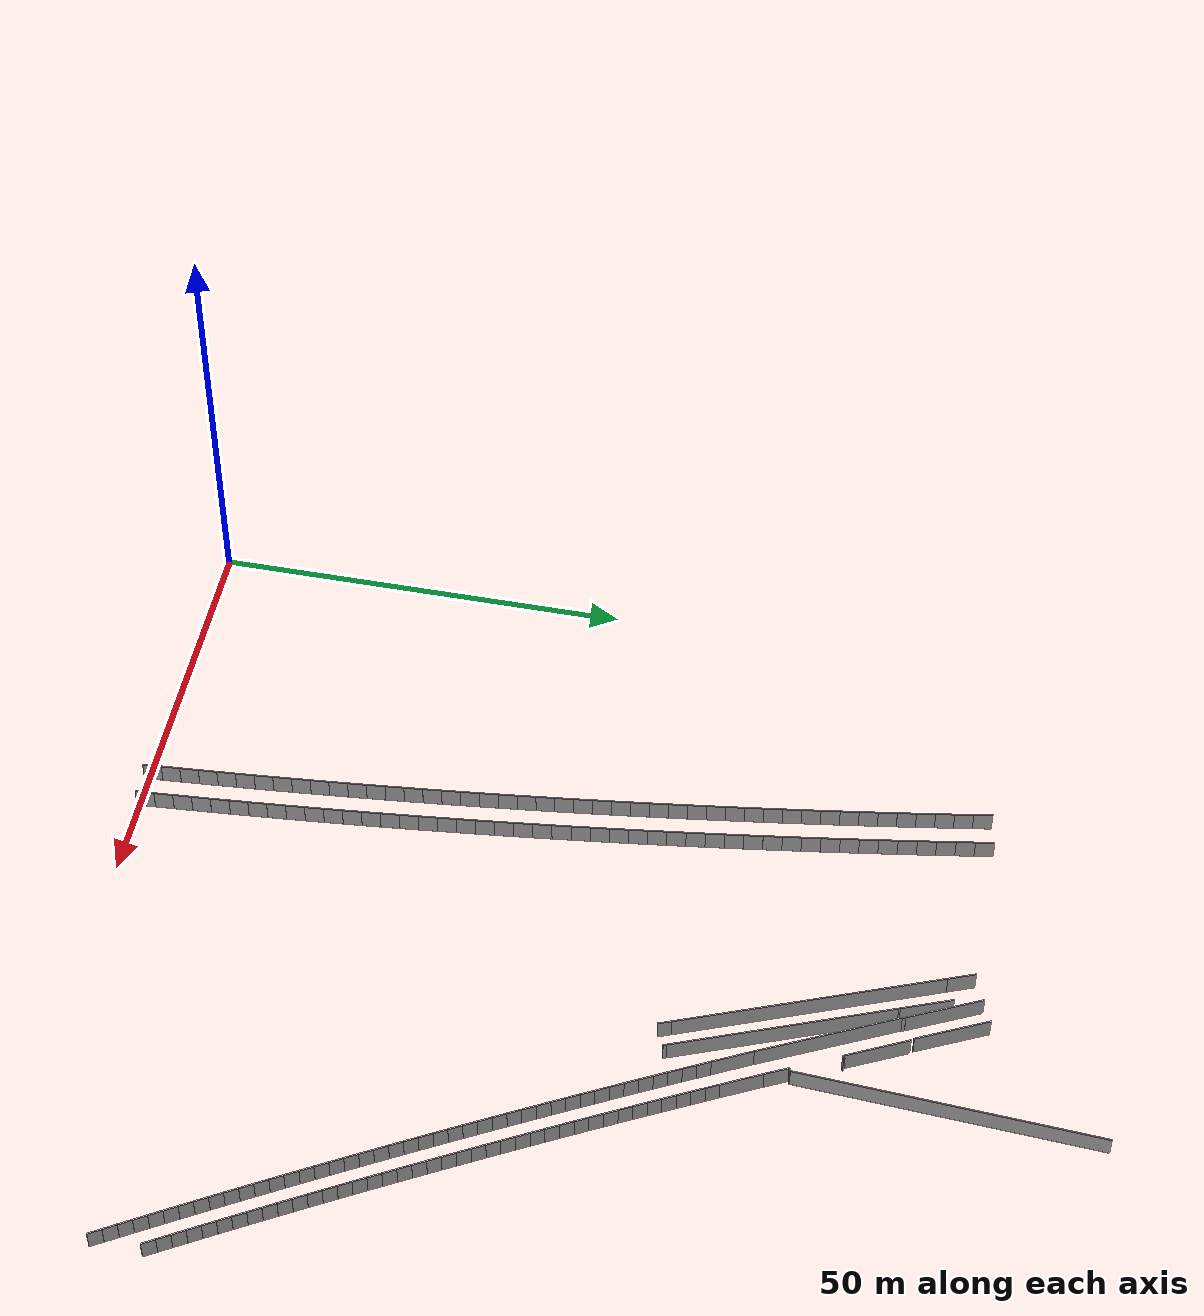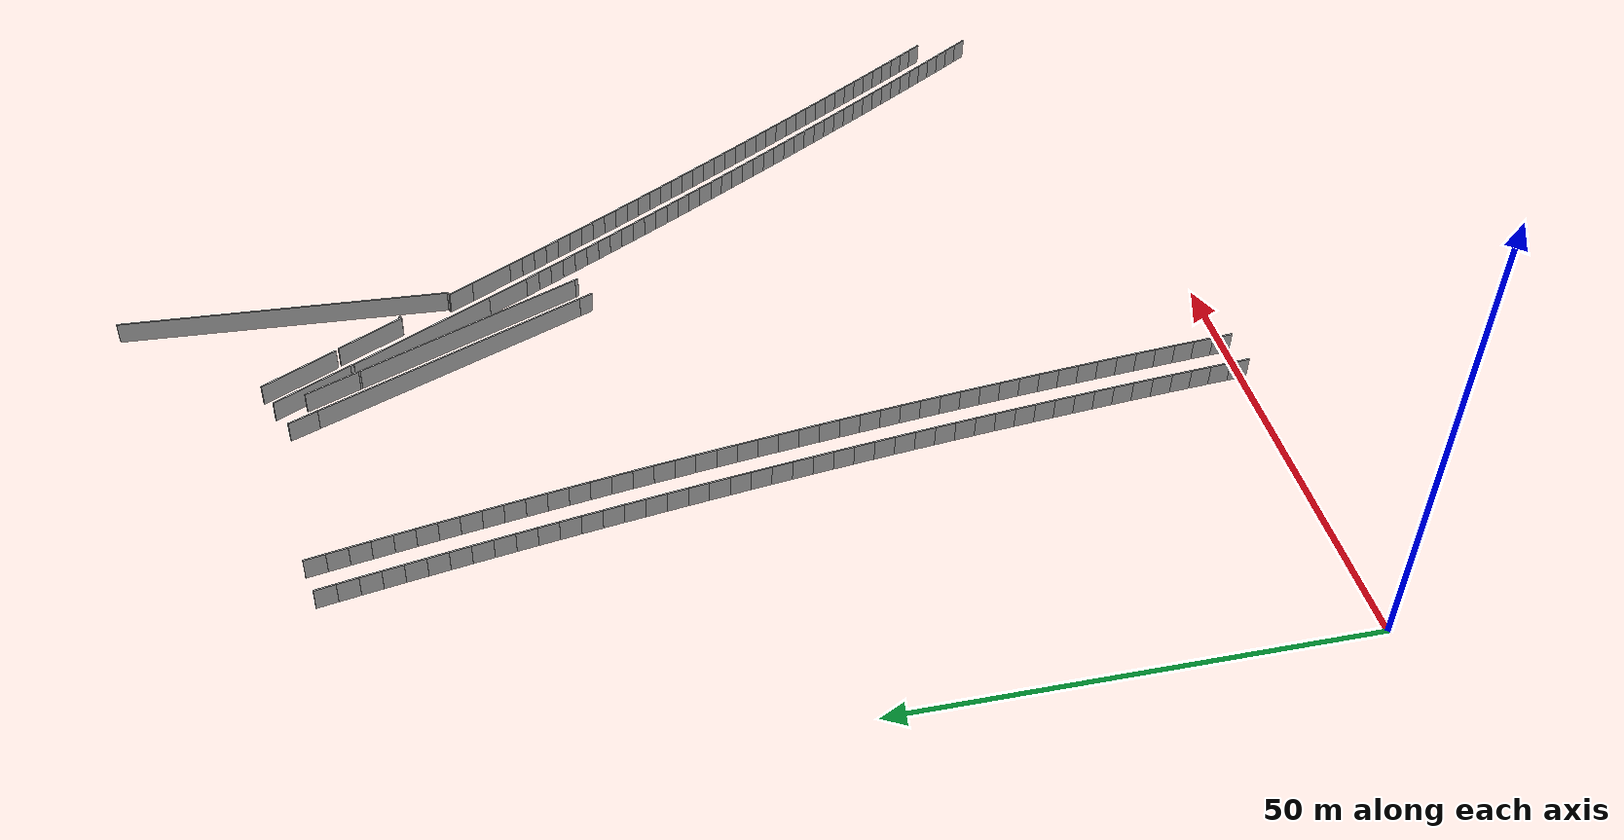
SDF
<?xml version="1.0" ?>
<sdf version="1.6">
  <model name="sps_2313">
    <pose frame="">0 0 0 0 -0 0</pose>
    <static>1</static>
    <self_collide>0</self_collide>
    <allow_auto_disable>0</allow_auto_disable>
    <link name="Wall324">
      <kinematic>0</kinematic>
      <gravity>1</gravity>
      <self_collide>0</self_collide>
      <collision name="collision">
        <geometry>
          <box>
            <size>0.205656 0.15 2.5</size>
          </box>
        </geometry>
        <pose frame="">0 0 0 0 -0 0</pose>
      </collision>
      <visual name="visual">
        <geometry>
          <box>
            <size>0.205656 0.15 2.5</size>
          </box>
        </geometry>
        <pose frame="">0 0 0 0 -0 0</pose>
        <cast_shadows>1</cast_shadows>
        <transparency>0.0</transparency>
      </visual>
      <pose frame="">53.7842 92.6752 1.25 0 0 -1.18594</pose>
    </link>
    <link name="Wall391">
      <kinematic>0</kinematic>
      <gravity>1</gravity>
      <self_collide>0</self_collide>
      <collision name="collision">
        <geometry>
          <box>
            <size>9.32021 0.15 2.5</size>
          </box>
        </geometry>
        <pose frame="">0 0 0 0 -0 0</pose>
      </collision>
      <visual name="visual">
        <geometry>
          <box>
            <size>9.32021 0.15 2.5</size>
          </box>
        </geometry>
        <pose frame="">0 0 0 0 -0 0</pose>
        <cast_shadows>1</cast_shadows>
        <transparency>0.0</transparency>
      </visual>
      <pose frame="">52.8168 97.721 1.25 0 0 -1.11304</pose>
    </link>
    <link name="Wall392">
      <kinematic>0</kinematic>
      <gravity>1</gravity>
      <self_collide>0</self_collide>
      <collision name="collision">
        <geometry>
          <box>
            <size>0.404799 0.15 2.5</size>
          </box>
        </geometry>
        <pose frame="">0 0 0 0 -0 0</pose>
      </collision>
      <visual name="visual">
        <geometry>
          <box>
            <size>0.404799 0.15 2.5</size>
          </box>
        </geometry>
        <pose frame="">0 0 0 0 -0 0</pose>
        <cast_shadows>1</cast_shadows>
        <transparency>0.0</transparency>
      </visual>
      <pose frame="">54.9357 93.3472 1.25 0 0 -1.27284</pose>
    </link>
    <link name="Wall393">
      <kinematic>0</kinematic>
      <gravity>1</gravity>
      <self_collide>0</self_collide>
      <collision name="collision">
        <geometry>
          <box>
            <size>9.08202 0.15 2.5</size>
          </box>
        </geometry>
        <pose frame="">0 0 0 0 -0 0</pose>
      </collision>
      <visual name="visual">
        <geometry>
          <box>
            <size>9.08202 0.15 2.5</size>
          </box>
        </geometry>
        <pose frame="">0 0 0 0 -0 0</pose>
        <cast_shadows>1</cast_shadows>
        <transparency>0.0</transparency>
      </visual>
      <pose frame="">55.5443 98.9319 1.25 0 0 -1.10902</pose>
    </link>
    <link name="Wall394">
      <kinematic>0</kinematic>
      <gravity>1</gravity>
      <self_collide>0</self_collide>
      <collision name="collision">
        <geometry>
          <box>
            <size>31.876 0.15 2.5</size>
          </box>
        </geometry>
        <pose frame="">0 0 0 0 -0 0</pose>
      </collision>
      <visual name="visual">
        <geometry>
          <box>
            <size>31.876 0.15 2.5</size>
          </box>
        </geometry>
        <pose frame="">0 0 0 0 -0 0</pose>
        <cast_shadows>1</cast_shadows>
        <transparency>0.0</transparency>
      </visual>
      <pose frame="">54.5925 82.6699 1.25 0 0 -1.18671</pose>
    </link>
    <link name="Wall395">
      <kinematic>0</kinematic>
      <gravity>1</gravity>
      <self_collide>0</self_collide>
      <collision name="collision">
        <geometry>
          <box>
            <size>1.59371 0.15 2.5</size>
          </box>
        </geometry>
        <pose frame="">0 0 0 0 -0 0</pose>
      </collision>
      <visual name="visual">
        <geometry>
          <box>
            <size>1.59371 0.15 2.5</size>
          </box>
        </geometry>
        <pose frame="">0 0 0 0 -0 0</pose>
        <cast_shadows>1</cast_shadows>
        <transparency>0.0</transparency>
      </visual>
      <pose frame="">60.8632 67.1543 1.25 0 0 -1.18671</pose>
    </link>
    <link name="Wall489">
      <kinematic>0</kinematic>
      <gravity>1</gravity>
      <self_collide>0</self_collide>
      <collision name="collision">
        <geometry>
          <box>
            <size>3.35308 0.15 2.5</size>
          </box>
        </geometry>
        <pose frame="">0 0 0 0 -0 0</pose>
      </collision>
      <visual name="visual">
        <geometry>
          <box>
            <size>3.35308 0.15 2.5</size>
          </box>
        </geometry>
        <pose frame="">0 0 0 0 -0 0</pose>
        <cast_shadows>1</cast_shadows>
        <transparency>0.0</transparency>
      </visual>
      <pose frame="">47.9918 99.0009 1.25 0 0 -1.18641</pose>
    </link>
    <link name="Wall664">
      <kinematic>0</kinematic>
      <gravity>1</gravity>
      <self_collide>0</self_collide>
      <collision name="collision">
        <geometry>
          <box>
            <size>6.2563 0.15 2.5</size>
          </box>
        </geometry>
        <pose frame="">0 0 0 0 -0 0</pose>
      </collision>
      <visual name="visual">
        <geometry>
          <box>
            <size>6.2563 0.15 2.5</size>
          </box>
        </geometry>
        <pose frame="">0 0 0 0 -0 0</pose>
        <cast_shadows>1</cast_shadows>
        <transparency>0.0</transparency>
      </visual>
      <pose frame="">52.5736 95.6708 1.25 0 0 -1.18676</pose>
    </link>
    <link name="Wall665">
      <kinematic>0</kinematic>
      <gravity>1</gravity>
      <self_collide>0</self_collide>
      <collision name="collision">
        <geometry>
          <box>
            <size>26.6269 0.15 2.5</size>
          </box>
        </geometry>
        <pose frame="">0 0 0 0 -0 0</pose>
      </collision>
      <visual name="visual">
        <geometry>
          <box>
            <size>26.6269 0.15 2.5</size>
          </box>
        </geometry>
        <pose frame="">0 0 0 0 -0 0</pose>
        <cast_shadows>1</cast_shadows>
        <transparency>0.0</transparency>
      </visual>
      <pose frame="">58.8117 80.2365 1.25 0 0 -1.1867</pose>
    </link>
    <link name="Wall666">
      <kinematic>0</kinematic>
      <gravity>1</gravity>
      <self_collide>0</self_collide>
      <collision name="collision">
        <geometry>
          <box>
            <size>0.380969 0.15 2.5</size>
          </box>
        </geometry>
        <pose frame="">0 0 0 0 -0 0</pose>
      </collision>
      <visual name="visual">
        <geometry>
          <box>
            <size>0.380969 0.15 2.5</size>
          </box>
        </geometry>
        <pose frame="">0 0 0 0 -0 0</pose>
        <cast_shadows>1</cast_shadows>
        <transparency>0.0</transparency>
      </visual>
      <pose frame="">63.8719 67.7165 1.25 0 0 -1.1867</pose>
    </link>
    <link name="Wall669">
      <kinematic>0</kinematic>
      <gravity>1</gravity>
      <self_collide>0</self_collide>
      <collision name="collision">
        <geometry>
          <box>
            <size>35.9252 0.15 2.5</size>
          </box>
        </geometry>
        <pose frame="">0 0 0 0 -0 0</pose>
      </collision>
      <visual name="visual">
        <geometry>
          <box>
            <size>35.9252 0.15 2.5</size>
          </box>
        </geometry>
        <pose frame="">0 0 0 0 -0 0</pose>
        <cast_shadows>1</cast_shadows>
        <transparency>0.0</transparency>
      </visual>
      <pose frame="">65.6361 99.9612 1.25 0 0 -1.62929</pose>
    </link>
    <link name="Wall4616">
      <kinematic>0</kinematic>
      <gravity>1</gravity>
      <self_collide>0</self_collide>
      <collision name="collision">
        <geometry>
          <box>
            <size>2.25473 0.15 2.5</size>
          </box>
        </geometry>
        <pose frame="">0 0 0 0 -0 0</pose>
      </collision>
      <visual name="visual">
        <geometry>
          <box>
            <size>2.25473 0.15 2.5</size>
          </box>
        </geometry>
        <pose frame="">0 0 0 0 -0 0</pose>
        <cast_shadows>1</cast_shadows>
        <transparency>0.0</transparency>
      </visual>
      <pose frame="">40.2125 0.755813 1.25 0 -0 1.63961</pose>
    </link>
    <link name="Wall4617">
      <kinematic>0</kinematic>
      <gravity>1</gravity>
      <self_collide>0</self_collide>
      <collision name="collision">
        <geometry>
          <box>
            <size>2.25463 0.15 2.5</size>
          </box>
        </geometry>
        <pose frame="">0 0 0 0 -0 0</pose>
      </collision>
      <visual name="visual">
        <geometry>
          <box>
            <size>2.25463 0.15 2.5</size>
          </box>
        </geometry>
        <pose frame="">0 0 0 0 -0 0</pose>
        <cast_shadows>1</cast_shadows>
        <transparency>0.0</transparency>
      </visual>
      <pose frame="">40.0551 3.00499 1.25 0 -0 1.64173</pose>
    </link>
    <link name="Wall4618">
      <kinematic>0</kinematic>
      <gravity>1</gravity>
      <self_collide>0</self_collide>
      <collision name="collision">
        <geometry>
          <box>
            <size>2.2545 0.15 2.5</size>
          </box>
        </geometry>
        <pose frame="">0 0 0 0 -0 0</pose>
      </collision>
      <visual name="visual">
        <geometry>
          <box>
            <size>2.2545 0.15 2.5</size>
          </box>
        </geometry>
        <pose frame="">0 0 0 0 -0 0</pose>
        <cast_shadows>1</cast_shadows>
        <transparency>0.0</transparency>
      </visual>
      <pose frame="">39.8924 5.25368 1.25 0 -0 1.64431</pose>
    </link>
    <link name="Wall4619">
      <kinematic>0</kinematic>
      <gravity>1</gravity>
      <self_collide>0</self_collide>
      <collision name="collision">
        <geometry>
          <box>
            <size>2.25469 0.15 2.5</size>
          </box>
        </geometry>
        <pose frame="">0 0 0 0 -0 0</pose>
      </collision>
      <visual name="visual">
        <geometry>
          <box>
            <size>2.25469 0.15 2.5</size>
          </box>
        </geometry>
        <pose frame="">0 0 0 0 -0 0</pose>
        <cast_shadows>1</cast_shadows>
        <transparency>0.0</transparency>
      </visual>
      <pose frame="">39.7244 7.502 1.25 0 -0 1.64653</pose>
    </link>
    <link name="Wall4620">
      <kinematic>0</kinematic>
      <gravity>1</gravity>
      <self_collide>0</self_collide>
      <collision name="collision">
        <geometry>
          <box>
            <size>2.2547 0.15 2.5</size>
          </box>
        </geometry>
        <pose frame="">0 0 0 0 -0 0</pose>
      </collision>
      <visual name="visual">
        <geometry>
          <box>
            <size>2.2547 0.15 2.5</size>
          </box>
        </geometry>
        <pose frame="">0 0 0 0 -0 0</pose>
        <cast_shadows>1</cast_shadows>
        <transparency>0.0</transparency>
      </visual>
      <pose frame="">39.551 9.75001 1.25 0 -0 1.64903</pose>
    </link>
    <link name="Wall4621">
      <kinematic>0</kinematic>
      <gravity>1</gravity>
      <self_collide>0</self_collide>
      <collision name="collision">
        <geometry>
          <box>
            <size>2.2545 0.15 2.5</size>
          </box>
        </geometry>
        <pose frame="">0 0 0 0 -0 0</pose>
      </collision>
      <visual name="visual">
        <geometry>
          <box>
            <size>2.2545 0.15 2.5</size>
          </box>
        </geometry>
        <pose frame="">0 0 0 0 -0 0</pose>
        <cast_shadows>1</cast_shadows>
        <transparency>0.0</transparency>
      </visual>
      <pose frame="">39.3722 11.9975 1.25 0 -0 1.65134</pose>
    </link>
    <link name="Wall4622">
      <kinematic>0</kinematic>
      <gravity>1</gravity>
      <self_collide>0</self_collide>
      <collision name="collision">
        <geometry>
          <box>
            <size>2.25452 0.15 2.5</size>
          </box>
        </geometry>
        <pose frame="">0 0 0 0 -0 0</pose>
      </collision>
      <visual name="visual">
        <geometry>
          <box>
            <size>2.25452 0.15 2.5</size>
          </box>
        </geometry>
        <pose frame="">0 0 0 0 -0 0</pose>
        <cast_shadows>1</cast_shadows>
        <transparency>0.0</transparency>
      </visual>
      <pose frame="">39.188 14.2445 1.25 0 -0 1.65376</pose>
    </link>
    <link name="Wall4623">
      <kinematic>0</kinematic>
      <gravity>1</gravity>
      <self_collide>0</self_collide>
      <collision name="collision">
        <geometry>
          <box>
            <size>2.25388 0.15 2.5</size>
          </box>
        </geometry>
        <pose frame="">0 0 0 0 -0 0</pose>
      </collision>
      <visual name="visual">
        <geometry>
          <box>
            <size>2.25388 0.15 2.5</size>
          </box>
        </geometry>
        <pose frame="">0 0 0 0 -0 0</pose>
        <cast_shadows>1</cast_shadows>
        <transparency>0.0</transparency>
      </visual>
      <pose frame="">38.9981 16.4907 1.25 0 -0 1.65653</pose>
    </link>
    <link name="Wall4624">
      <kinematic>0</kinematic>
      <gravity>1</gravity>
      <self_collide>0</self_collide>
      <collision name="collision">
        <geometry>
          <box>
            <size>2.25489 0.15 2.5</size>
          </box>
        </geometry>
        <pose frame="">0 0 0 0 -0 0</pose>
      </collision>
      <visual name="visual">
        <geometry>
          <box>
            <size>2.25489 0.15 2.5</size>
          </box>
        </geometry>
        <pose frame="">0 0 0 0 -0 0</pose>
        <cast_shadows>1</cast_shadows>
        <transparency>0.0</transparency>
      </visual>
      <pose frame="">38.8028 18.7366 1.25 0 -0 1.65853</pose>
    </link>
    <link name="Wall4625">
      <kinematic>0</kinematic>
      <gravity>1</gravity>
      <self_collide>0</self_collide>
      <collision name="collision">
        <geometry>
          <box>
            <size>2.25432 0.15 2.5</size>
          </box>
        </geometry>
        <pose frame="">0 0 0 0 -0 0</pose>
      </collision>
      <visual name="visual">
        <geometry>
          <box>
            <size>2.25432 0.15 2.5</size>
          </box>
        </geometry>
        <pose frame="">0 0 0 0 -0 0</pose>
        <cast_shadows>1</cast_shadows>
        <transparency>0.0</transparency>
      </visual>
      <pose frame="">38.6027 20.9823 1.25 0 -0 1.66089</pose>
    </link>
    <link name="Wall4626">
      <kinematic>0</kinematic>
      <gravity>1</gravity>
      <self_collide>0</self_collide>
      <collision name="collision">
        <geometry>
          <box>
            <size>2.25487 0.15 2.5</size>
          </box>
        </geometry>
        <pose frame="">0 0 0 0 -0 0</pose>
      </collision>
      <visual name="visual">
        <geometry>
          <box>
            <size>2.25487 0.15 2.5</size>
          </box>
        </geometry>
        <pose frame="">0 0 0 0 -0 0</pose>
        <cast_shadows>1</cast_shadows>
        <transparency>0.0</transparency>
      </visual>
      <pose frame="">38.3971 23.2275 1.25 0 -0 1.66326</pose>
    </link>
    <link name="Wall4627">
      <kinematic>0</kinematic>
      <gravity>1</gravity>
      <self_collide>0</self_collide>
      <collision name="collision">
        <geometry>
          <box>
            <size>2.25453 0.15 2.5</size>
          </box>
        </geometry>
        <pose frame="">0 0 0 0 -0 0</pose>
      </collision>
      <visual name="visual">
        <geometry>
          <box>
            <size>2.25453 0.15 2.5</size>
          </box>
        </geometry>
        <pose frame="">0 0 0 0 -0 0</pose>
        <cast_shadows>1</cast_shadows>
        <transparency>0.0</transparency>
      </visual>
      <pose frame="">38.1862 25.4723 1.25 0 -0 1.66569</pose>
    </link>
    <link name="Wall4628">
      <kinematic>0</kinematic>
      <gravity>1</gravity>
      <self_collide>0</self_collide>
      <collision name="collision">
        <geometry>
          <box>
            <size>2.25441 0.15 2.5</size>
          </box>
        </geometry>
        <pose frame="">0 0 0 0 -0 0</pose>
      </collision>
      <visual name="visual">
        <geometry>
          <box>
            <size>2.25441 0.15 2.5</size>
          </box>
        </geometry>
        <pose frame="">0 0 0 0 -0 0</pose>
        <cast_shadows>1</cast_shadows>
        <transparency>0.0</transparency>
      </visual>
      <pose frame="">37.9701 27.7164 1.25 0 -0 1.66798</pose>
    </link>
    <link name="Wall4629">
      <kinematic>0</kinematic>
      <gravity>1</gravity>
      <self_collide>0</self_collide>
      <collision name="collision">
        <geometry>
          <box>
            <size>2.25475 0.15 2.5</size>
          </box>
        </geometry>
        <pose frame="">0 0 0 0 -0 0</pose>
      </collision>
      <visual name="visual">
        <geometry>
          <box>
            <size>2.25475 0.15 2.5</size>
          </box>
        </geometry>
        <pose frame="">0 0 0 0 -0 0</pose>
        <cast_shadows>1</cast_shadows>
        <transparency>0.0</transparency>
      </visual>
      <pose frame="">37.7487 29.9601 1.25 0 -0 1.67031</pose>
    </link>
    <link name="Wall4630">
      <kinematic>0</kinematic>
      <gravity>1</gravity>
      <self_collide>0</self_collide>
      <collision name="collision">
        <geometry>
          <box>
            <size>2.25458 0.15 2.5</size>
          </box>
        </geometry>
        <pose frame="">0 0 0 0 -0 0</pose>
      </collision>
      <visual name="visual">
        <geometry>
          <box>
            <size>2.25458 0.15 2.5</size>
          </box>
        </geometry>
        <pose frame="">0 0 0 0 -0 0</pose>
        <cast_shadows>1</cast_shadows>
        <transparency>0.0</transparency>
      </visual>
      <pose frame="">37.5219 32.2033 1.25 0 -0 1.67282</pose>
    </link>
    <link name="Wall4631">
      <kinematic>0</kinematic>
      <gravity>1</gravity>
      <self_collide>0</self_collide>
      <collision name="collision">
        <geometry>
          <box>
            <size>2.25481 0.15 2.5</size>
          </box>
        </geometry>
        <pose frame="">0 0 0 0 -0 0</pose>
      </collision>
      <visual name="visual">
        <geometry>
          <box>
            <size>2.25481 0.15 2.5</size>
          </box>
        </geometry>
        <pose frame="">0 0 0 0 -0 0</pose>
        <cast_shadows>1</cast_shadows>
        <transparency>0.0</transparency>
      </visual>
      <pose frame="">37.2897 34.446 1.25 0 -0 1.67512</pose>
    </link>
    <link name="Wall4632">
      <kinematic>0</kinematic>
      <gravity>1</gravity>
      <self_collide>0</self_collide>
      <collision name="collision">
        <geometry>
          <box>
            <size>2.25463 0.15 2.5</size>
          </box>
        </geometry>
        <pose frame="">0 0 0 0 -0 0</pose>
      </collision>
      <visual name="visual">
        <geometry>
          <box>
            <size>2.25463 0.15 2.5</size>
          </box>
        </geometry>
        <pose frame="">0 0 0 0 -0 0</pose>
        <cast_shadows>1</cast_shadows>
        <transparency>0.0</transparency>
      </visual>
      <pose frame="">37.0523 36.6882 1.25 0 -0 1.67744</pose>
    </link>
    <link name="Wall4633">
      <kinematic>0</kinematic>
      <gravity>1</gravity>
      <self_collide>0</self_collide>
      <collision name="collision">
        <geometry>
          <box>
            <size>2.25465 0.15 2.5</size>
          </box>
        </geometry>
        <pose frame="">0 0 0 0 -0 0</pose>
      </collision>
      <visual name="visual">
        <geometry>
          <box>
            <size>2.25465 0.15 2.5</size>
          </box>
        </geometry>
        <pose frame="">0 0 0 0 -0 0</pose>
        <cast_shadows>1</cast_shadows>
        <transparency>0.0</transparency>
      </visual>
      <pose frame="">36.8094 38.9297 1.25 0 -0 1.68003</pose>
    </link>
    <link name="Wall4634">
      <kinematic>0</kinematic>
      <gravity>1</gravity>
      <self_collide>0</self_collide>
      <collision name="collision">
        <geometry>
          <box>
            <size>2.25457 0.15 2.5</size>
          </box>
        </geometry>
        <pose frame="">0 0 0 0 -0 0</pose>
      </collision>
      <visual name="visual">
        <geometry>
          <box>
            <size>2.25457 0.15 2.5</size>
          </box>
        </geometry>
        <pose frame="">0 0 0 0 -0 0</pose>
        <cast_shadows>1</cast_shadows>
        <transparency>0.0</transparency>
      </visual>
      <pose frame="">36.5612 41.1706 1.25 0 -0 1.68218</pose>
    </link>
    <link name="Wall4635">
      <kinematic>0</kinematic>
      <gravity>1</gravity>
      <self_collide>0</self_collide>
      <collision name="collision">
        <geometry>
          <box>
            <size>2.2546 0.15 2.5</size>
          </box>
        </geometry>
        <pose frame="">0 0 0 0 -0 0</pose>
      </collision>
      <visual name="visual">
        <geometry>
          <box>
            <size>2.2546 0.15 2.5</size>
          </box>
        </geometry>
        <pose frame="">0 0 0 0 -0 0</pose>
        <cast_shadows>1</cast_shadows>
        <transparency>0.0</transparency>
      </visual>
      <pose frame="">36.3078 43.4109 1.25 0 -0 1.68469</pose>
    </link>
    <link name="Wall4636">
      <kinematic>0</kinematic>
      <gravity>1</gravity>
      <self_collide>0</self_collide>
      <collision name="collision">
        <geometry>
          <box>
            <size>2.25459 0.15 2.5</size>
          </box>
        </geometry>
        <pose frame="">0 0 0 0 -0 0</pose>
      </collision>
      <visual name="visual">
        <geometry>
          <box>
            <size>2.25459 0.15 2.5</size>
          </box>
        </geometry>
        <pose frame="">0 0 0 0 -0 0</pose>
        <cast_shadows>1</cast_shadows>
        <transparency>0.0</transparency>
      </visual>
      <pose frame="">36.0489 45.6506 1.25 0 -0 1.68701</pose>
    </link>
    <link name="Wall4637">
      <kinematic>0</kinematic>
      <gravity>1</gravity>
      <self_collide>0</self_collide>
      <collision name="collision">
        <geometry>
          <box>
            <size>2.25467 0.15 2.5</size>
          </box>
        </geometry>
        <pose frame="">0 0 0 0 -0 0</pose>
      </collision>
      <visual name="visual">
        <geometry>
          <box>
            <size>2.25467 0.15 2.5</size>
          </box>
        </geometry>
        <pose frame="">0 0 0 0 -0 0</pose>
        <cast_shadows>1</cast_shadows>
        <transparency>0.0</transparency>
      </visual>
      <pose frame="">35.7848 47.8897 1.25 0 -0 1.6894</pose>
    </link>
    <link name="Wall4638">
      <kinematic>0</kinematic>
      <gravity>1</gravity>
      <self_collide>0</self_collide>
      <collision name="collision">
        <geometry>
          <box>
            <size>2.25393 0.15 2.5</size>
          </box>
        </geometry>
        <pose frame="">0 0 0 0 -0 0</pose>
      </collision>
      <visual name="visual">
        <geometry>
          <box>
            <size>2.25393 0.15 2.5</size>
          </box>
        </geometry>
        <pose frame="">0 0 0 0 -0 0</pose>
        <cast_shadows>1</cast_shadows>
        <transparency>0.0</transparency>
      </visual>
      <pose frame="">35.5151 50.1278 1.25 0 -0 1.69211</pose>
    </link>
    <link name="Wall4639">
      <kinematic>0</kinematic>
      <gravity>1</gravity>
      <self_collide>0</self_collide>
      <collision name="collision">
        <geometry>
          <box>
            <size>2.25438 0.15 2.5</size>
          </box>
        </geometry>
        <pose frame="">0 0 0 0 -0 0</pose>
      </collision>
      <visual name="visual">
        <geometry>
          <box>
            <size>2.25438 0.15 2.5</size>
          </box>
        </geometry>
        <pose frame="">0 0 0 0 -0 0</pose>
        <cast_shadows>1</cast_shadows>
        <transparency>0.0</transparency>
      </visual>
      <pose frame="">35.24 52.3651 1.25 0 -0 1.69416</pose>
    </link>
    <link name="Wall4640">
      <kinematic>0</kinematic>
      <gravity>1</gravity>
      <self_collide>0</self_collide>
      <collision name="collision">
        <geometry>
          <box>
            <size>2.25481 0.15 2.5</size>
          </box>
        </geometry>
        <pose frame="">0 0 0 0 -0 0</pose>
      </collision>
      <visual name="visual">
        <geometry>
          <box>
            <size>2.25481 0.15 2.5</size>
          </box>
        </geometry>
        <pose frame="">0 0 0 0 -0 0</pose>
        <cast_shadows>1</cast_shadows>
        <transparency>0.0</transparency>
      </visual>
      <pose frame="">34.9599 54.6022 1.25 0 -0 1.69656</pose>
    </link>
    <link name="Wall4641">
      <kinematic>0</kinematic>
      <gravity>1</gravity>
      <self_collide>0</self_collide>
      <collision name="collision">
        <geometry>
          <box>
            <size>2.25443 0.15 2.5</size>
          </box>
        </geometry>
        <pose frame="">0 0 0 0 -0 0</pose>
      </collision>
      <visual name="visual">
        <geometry>
          <box>
            <size>2.25443 0.15 2.5</size>
          </box>
        </geometry>
        <pose frame="">0 0 0 0 -0 0</pose>
        <cast_shadows>1</cast_shadows>
        <transparency>0.0</transparency>
      </visual>
      <pose frame="">34.6745 56.8387 1.25 0 -0 1.69888</pose>
    </link>
    <link name="Wall4642">
      <kinematic>0</kinematic>
      <gravity>1</gravity>
      <self_collide>0</self_collide>
      <collision name="collision">
        <geometry>
          <box>
            <size>2.25477 0.15 2.5</size>
          </box>
        </geometry>
        <pose frame="">0 0 0 0 -0 0</pose>
      </collision>
      <visual name="visual">
        <geometry>
          <box>
            <size>2.25477 0.15 2.5</size>
          </box>
        </geometry>
        <pose frame="">0 0 0 0 -0 0</pose>
        <cast_shadows>1</cast_shadows>
        <transparency>0.0</transparency>
      </visual>
      <pose frame="">34.3838 59.0745 1.25 0 -0 1.70129</pose>
    </link>
    <link name="Wall4643">
      <kinematic>0</kinematic>
      <gravity>1</gravity>
      <self_collide>0</self_collide>
      <collision name="collision">
        <geometry>
          <box>
            <size>2.25467 0.15 2.5</size>
          </box>
        </geometry>
        <pose frame="">0 0 0 0 -0 0</pose>
      </collision>
      <visual name="visual">
        <geometry>
          <box>
            <size>2.25467 0.15 2.5</size>
          </box>
        </geometry>
        <pose frame="">0 0 0 0 -0 0</pose>
        <cast_shadows>1</cast_shadows>
        <transparency>0.0</transparency>
      </visual>
      <pose frame="">34.0878 61.3097 1.25 0 -0 1.70364</pose>
    </link>
    <link name="Wall4644">
      <kinematic>0</kinematic>
      <gravity>1</gravity>
      <self_collide>0</self_collide>
      <collision name="collision">
        <geometry>
          <box>
            <size>2.25459 0.15 2.5</size>
          </box>
        </geometry>
        <pose frame="">0 0 0 0 -0 0</pose>
      </collision>
      <visual name="visual">
        <geometry>
          <box>
            <size>2.25459 0.15 2.5</size>
          </box>
        </geometry>
        <pose frame="">0 0 0 0 -0 0</pose>
        <cast_shadows>1</cast_shadows>
        <transparency>0.0</transparency>
      </visual>
      <pose frame="">33.7865 63.5441 1.25 0 -0 1.70602</pose>
    </link>
    <link name="Wall4645">
      <kinematic>0</kinematic>
      <gravity>1</gravity>
      <self_collide>0</self_collide>
      <collision name="collision">
        <geometry>
          <box>
            <size>2.25452 0.15 2.5</size>
          </box>
        </geometry>
        <pose frame="">0 0 0 0 -0 0</pose>
      </collision>
      <visual name="visual">
        <geometry>
          <box>
            <size>2.25452 0.15 2.5</size>
          </box>
        </geometry>
        <pose frame="">0 0 0 0 -0 0</pose>
        <cast_shadows>1</cast_shadows>
        <transparency>0.0</transparency>
      </visual>
      <pose frame="">33.4799 65.7777 1.25 0 -0 1.70838</pose>
    </link>
    <link name="Wall4646">
      <kinematic>0</kinematic>
      <gravity>1</gravity>
      <self_collide>0</self_collide>
      <collision name="collision">
        <geometry>
          <box>
            <size>2.25467 0.15 2.5</size>
          </box>
        </geometry>
        <pose frame="">0 0 0 0 -0 0</pose>
      </collision>
      <visual name="visual">
        <geometry>
          <box>
            <size>2.25467 0.15 2.5</size>
          </box>
        </geometry>
        <pose frame="">0 0 0 0 -0 0</pose>
        <cast_shadows>1</cast_shadows>
        <transparency>0.0</transparency>
      </visual>
      <pose frame="">33.168 68.0106 1.25 0 -0 1.7108</pose>
    </link>
    <link name="Wall4647">
      <kinematic>0</kinematic>
      <gravity>1</gravity>
      <self_collide>0</self_collide>
      <collision name="collision">
        <geometry>
          <box>
            <size>2.25464 0.15 2.5</size>
          </box>
        </geometry>
        <pose frame="">0 0 0 0 -0 0</pose>
      </collision>
      <visual name="visual">
        <geometry>
          <box>
            <size>2.25464 0.15 2.5</size>
          </box>
        </geometry>
        <pose frame="">0 0 0 0 -0 0</pose>
        <cast_shadows>1</cast_shadows>
        <transparency>0.0</transparency>
      </visual>
      <pose frame="">32.8506 70.2428 1.25 0 -0 1.71321</pose>
    </link>
    <link name="Wall4648">
      <kinematic>0</kinematic>
      <gravity>1</gravity>
      <self_collide>0</self_collide>
      <collision name="collision">
        <geometry>
          <box>
            <size>2.25478 0.15 2.5</size>
          </box>
        </geometry>
        <pose frame="">0 0 0 0 -0 0</pose>
      </collision>
      <visual name="visual">
        <geometry>
          <box>
            <size>2.25478 0.15 2.5</size>
          </box>
        </geometry>
        <pose frame="">0 0 0 0 -0 0</pose>
        <cast_shadows>1</cast_shadows>
        <transparency>0.0</transparency>
      </visual>
      <pose frame="">32.528 72.4743 1.25 0 -0 1.71553</pose>
    </link>
    <link name="Wall4649">
      <kinematic>0</kinematic>
      <gravity>1</gravity>
      <self_collide>0</self_collide>
      <collision name="collision">
        <geometry>
          <box>
            <size>2.25468 0.15 2.5</size>
          </box>
        </geometry>
        <pose frame="">0 0 0 0 -0 0</pose>
      </collision>
      <visual name="visual">
        <geometry>
          <box>
            <size>2.25468 0.15 2.5</size>
          </box>
        </geometry>
        <pose frame="">0 0 0 0 -0 0</pose>
        <cast_shadows>1</cast_shadows>
        <transparency>0.0</transparency>
      </visual>
      <pose frame="">32.2002 74.7051 1.25 0 -0 1.71786</pose>
    </link>
    <link name="Wall4650">
      <kinematic>0</kinematic>
      <gravity>1</gravity>
      <self_collide>0</self_collide>
      <collision name="collision">
        <geometry>
          <box>
            <size>2.25416 0.15 2.5</size>
          </box>
        </geometry>
        <pose frame="">0 0 0 0 -0 0</pose>
      </collision>
      <visual name="visual">
        <geometry>
          <box>
            <size>2.25416 0.15 2.5</size>
          </box>
        </geometry>
        <pose frame="">0 0 0 0 -0 0</pose>
        <cast_shadows>1</cast_shadows>
        <transparency>0.0</transparency>
      </visual>
      <pose frame="">31.8671 76.9348 1.25 0 -0 1.72033</pose>
    </link>
    <link name="Wall4651">
      <kinematic>0</kinematic>
      <gravity>1</gravity>
      <self_collide>0</self_collide>
      <collision name="collision">
        <geometry>
          <box>
            <size>2.2546 0.15 2.5</size>
          </box>
        </geometry>
        <pose frame="">0 0 0 0 -0 0</pose>
      </collision>
      <visual name="visual">
        <geometry>
          <box>
            <size>2.2546 0.15 2.5</size>
          </box>
        </geometry>
        <pose frame="">0 0 0 0 -0 0</pose>
        <cast_shadows>1</cast_shadows>
        <transparency>0.0</transparency>
      </visual>
      <pose frame="">31.5286 79.1636 1.25 0 -0 1.72271</pose>
    </link>
    <link name="Wall4652">
      <kinematic>0</kinematic>
      <gravity>1</gravity>
      <self_collide>0</self_collide>
      <collision name="collision">
        <geometry>
          <box>
            <size>2.25404 0.15 2.5</size>
          </box>
        </geometry>
        <pose frame="">0 0 0 0 -0 0</pose>
      </collision>
      <visual name="visual">
        <geometry>
          <box>
            <size>2.25404 0.15 2.5</size>
          </box>
        </geometry>
        <pose frame="">0 0 0 0 -0 0</pose>
        <cast_shadows>1</cast_shadows>
        <transparency>0.0</transparency>
      </visual>
      <pose frame="">31.1846 81.3915 1.25 0 -0 1.72535</pose>
    </link>
    <link name="Wall4653">
      <kinematic>0</kinematic>
      <gravity>1</gravity>
      <self_collide>0</self_collide>
      <collision name="collision">
        <geometry>
          <box>
            <size>2.25482 0.15 2.5</size>
          </box>
        </geometry>
        <pose frame="">0 0 0 0 -0 0</pose>
      </collision>
      <visual name="visual">
        <geometry>
          <box>
            <size>2.25482 0.15 2.5</size>
          </box>
        </geometry>
        <pose frame="">0 0 0 0 -0 0</pose>
        <cast_shadows>1</cast_shadows>
        <transparency>0.0</transparency>
      </visual>
      <pose frame="">30.8353 83.6187 1.25 0 -0 1.72738</pose>
    </link>
    <link name="Wall4654">
      <kinematic>0</kinematic>
      <gravity>1</gravity>
      <self_collide>0</self_collide>
      <collision name="collision">
        <geometry>
          <box>
            <size>2.25464 0.15 2.5</size>
          </box>
        </geometry>
        <pose frame="">0 0 0 0 -0 0</pose>
      </collision>
      <visual name="visual">
        <geometry>
          <box>
            <size>2.25464 0.15 2.5</size>
          </box>
        </geometry>
        <pose frame="">0 0 0 0 -0 0</pose>
        <cast_shadows>1</cast_shadows>
        <transparency>0.0</transparency>
      </visual>
      <pose frame="">30.4809 85.8454 1.25 0 -0 1.7298</pose>
    </link>
    <link name="Wall4655">
      <kinematic>0</kinematic>
      <gravity>1</gravity>
      <self_collide>0</self_collide>
      <collision name="collision">
        <geometry>
          <box>
            <size>2.25447 0.15 2.5</size>
          </box>
        </geometry>
        <pose frame="">0 0 0 0 -0 0</pose>
      </collision>
      <visual name="visual">
        <geometry>
          <box>
            <size>2.25447 0.15 2.5</size>
          </box>
        </geometry>
        <pose frame="">0 0 0 0 -0 0</pose>
        <cast_shadows>1</cast_shadows>
        <transparency>0.0</transparency>
      </visual>
      <pose frame="">30.1213 88.0711 1.25 0 -0 1.73223</pose>
    </link>
    <link name="Wall4656">
      <kinematic>0</kinematic>
      <gravity>1</gravity>
      <self_collide>0</self_collide>
      <collision name="collision">
        <geometry>
          <box>
            <size>2.2546 0.15 2.5</size>
          </box>
        </geometry>
        <pose frame="">0 0 0 0 -0 0</pose>
      </collision>
      <visual name="visual">
        <geometry>
          <box>
            <size>2.2546 0.15 2.5</size>
          </box>
        </geometry>
        <pose frame="">0 0 0 0 -0 0</pose>
        <cast_shadows>1</cast_shadows>
        <transparency>0.0</transparency>
      </visual>
      <pose frame="">29.7563 90.2959 1.25 0 -0 1.73458</pose>
    </link>
    <link name="Wall4657">
      <kinematic>0</kinematic>
      <gravity>1</gravity>
      <self_collide>0</self_collide>
      <collision name="collision">
        <geometry>
          <box>
            <size>2.25458 0.15 2.5</size>
          </box>
        </geometry>
        <pose frame="">0 0 0 0 -0 0</pose>
      </collision>
      <visual name="visual">
        <geometry>
          <box>
            <size>2.25458 0.15 2.5</size>
          </box>
        </geometry>
        <pose frame="">0 0 0 0 -0 0</pose>
        <cast_shadows>1</cast_shadows>
        <transparency>0.0</transparency>
      </visual>
      <pose frame="">29.3862 92.5199 1.25 0 -0 1.73683</pose>
    </link>
    <link name="Wall4658">
      <kinematic>0</kinematic>
      <gravity>1</gravity>
      <self_collide>0</self_collide>
      <collision name="collision">
        <geometry>
          <box>
            <size>2.25482 0.15 2.5</size>
          </box>
        </geometry>
        <pose frame="">0 0 0 0 -0 0</pose>
      </collision>
      <visual name="visual">
        <geometry>
          <box>
            <size>2.25482 0.15 2.5</size>
          </box>
        </geometry>
        <pose frame="">0 0 0 0 -0 0</pose>
        <cast_shadows>1</cast_shadows>
        <transparency>0.0</transparency>
      </visual>
      <pose frame="">29.0106 94.7431 1.25 0 -0 1.73942</pose>
    </link>
    <link name="Wall4659">
      <kinematic>0</kinematic>
      <gravity>1</gravity>
      <self_collide>0</self_collide>
      <collision name="collision">
        <geometry>
          <box>
            <size>2.2546 0.15 2.5</size>
          </box>
        </geometry>
        <pose frame="">0 0 0 0 -0 0</pose>
      </collision>
      <visual name="visual">
        <geometry>
          <box>
            <size>2.2546 0.15 2.5</size>
          </box>
        </geometry>
        <pose frame="">0 0 0 0 -0 0</pose>
        <cast_shadows>1</cast_shadows>
        <transparency>0.0</transparency>
      </visual>
      <pose frame="">28.6298 96.9654 1.25 0 -0 1.74158</pose>
    </link>
    <link name="Wall4660">
      <kinematic>0</kinematic>
      <gravity>1</gravity>
      <self_collide>0</self_collide>
      <collision name="collision">
        <geometry>
          <box>
            <size>2.25451 0.15 2.5</size>
          </box>
        </geometry>
        <pose frame="">0 0 0 0 -0 0</pose>
      </collision>
      <visual name="visual">
        <geometry>
          <box>
            <size>2.25451 0.15 2.5</size>
          </box>
        </geometry>
        <pose frame="">0 0 0 0 -0 0</pose>
        <cast_shadows>1</cast_shadows>
        <transparency>0.0</transparency>
      </visual>
      <pose frame="">28.2439 99.1867 1.25 0 -0 1.74403</pose>
    </link>
    <link name="Wall6341">
      <kinematic>0</kinematic>
      <gravity>1</gravity>
      <self_collide>0</self_collide>
      <collision name="collision">
        <geometry>
          <box>
            <size>2.24467 0.15 2.5</size>
          </box>
        </geometry>
        <pose frame="">0 0 0 0 -0 0</pose>
      </collision>
      <visual name="visual">
        <geometry>
          <box>
            <size>2.24467 0.15 2.5</size>
          </box>
        </geometry>
        <pose frame="">0 0 0 0 -0 0</pose>
        <cast_shadows>1</cast_shadows>
        <transparency>0.0</transparency>
      </visual>
      <pose frame="">36.0831 0.471389 1.25 0 -0 1.63945</pose>
    </link>
    <link name="Wall6342">
      <kinematic>0</kinematic>
      <gravity>1</gravity>
      <self_collide>0</self_collide>
      <collision name="collision">
        <geometry>
          <box>
            <size>2.24486 0.15 2.5</size>
          </box>
        </geometry>
        <pose frame="">0 0 0 0 -0 0</pose>
      </collision>
      <visual name="visual">
        <geometry>
          <box>
            <size>2.24486 0.15 2.5</size>
          </box>
        </geometry>
        <pose frame="">0 0 0 0 -0 0</pose>
        <cast_shadows>1</cast_shadows>
        <transparency>0.0</transparency>
      </visual>
      <pose frame="">35.9264 2.71068 1.25 0 -0 1.64187</pose>
    </link>
    <link name="Wall6343">
      <kinematic>0</kinematic>
      <gravity>1</gravity>
      <self_collide>0</self_collide>
      <collision name="collision">
        <geometry>
          <box>
            <size>2.24507 0.15 2.5</size>
          </box>
        </geometry>
        <pose frame="">0 0 0 0 -0 0</pose>
      </collision>
      <visual name="visual">
        <geometry>
          <box>
            <size>2.24507 0.15 2.5</size>
          </box>
        </geometry>
        <pose frame="">0 0 0 0 -0 0</pose>
        <cast_shadows>1</cast_shadows>
        <transparency>0.0</transparency>
      </visual>
      <pose frame="">35.7642 4.94978 1.25 0 -0 1.64427</pose>
    </link>
    <link name="Wall6344">
      <kinematic>0</kinematic>
      <gravity>1</gravity>
      <self_collide>0</self_collide>
      <collision name="collision">
        <geometry>
          <box>
            <size>2.24467 0.15 2.5</size>
          </box>
        </geometry>
        <pose frame="">0 0 0 0 -0 0</pose>
      </collision>
      <visual name="visual">
        <geometry>
          <box>
            <size>2.24467 0.15 2.5</size>
          </box>
        </geometry>
        <pose frame="">0 0 0 0 -0 0</pose>
        <cast_shadows>1</cast_shadows>
        <transparency>0.0</transparency>
      </visual>
      <pose frame="">35.5969 7.1884 1.25 0 -0 1.6466</pose>
    </link>
    <link name="Wall6345">
      <kinematic>0</kinematic>
      <gravity>1</gravity>
      <self_collide>0</self_collide>
      <collision name="collision">
        <geometry>
          <box>
            <size>2.24466 0.15 2.5</size>
          </box>
        </geometry>
        <pose frame="">0 0 0 0 -0 0</pose>
      </collision>
      <visual name="visual">
        <geometry>
          <box>
            <size>2.24466 0.15 2.5</size>
          </box>
        </geometry>
        <pose frame="">0 0 0 0 -0 0</pose>
        <cast_shadows>1</cast_shadows>
        <transparency>0.0</transparency>
      </visual>
      <pose frame="">35.4242 9.42641 1.25 0 -0 1.64902</pose>
    </link>
    <link name="Wall6346">
      <kinematic>0</kinematic>
      <gravity>1</gravity>
      <self_collide>0</self_collide>
      <collision name="collision">
        <geometry>
          <box>
            <size>2.24489 0.15 2.5</size>
          </box>
        </geometry>
        <pose frame="">0 0 0 0 -0 0</pose>
      </collision>
      <visual name="visual">
        <geometry>
          <box>
            <size>2.24489 0.15 2.5</size>
          </box>
        </geometry>
        <pose frame="">0 0 0 0 -0 0</pose>
        <cast_shadows>1</cast_shadows>
        <transparency>0.0</transparency>
      </visual>
      <pose frame="">35.2461 11.6641 1.25 0 -0 1.65133</pose>
    </link>
    <link name="Wall6347">
      <kinematic>0</kinematic>
      <gravity>1</gravity>
      <self_collide>0</self_collide>
      <collision name="collision">
        <geometry>
          <box>
            <size>2.2449 0.15 2.5</size>
          </box>
        </geometry>
        <pose frame="">0 0 0 0 -0 0</pose>
      </collision>
      <visual name="visual">
        <geometry>
          <box>
            <size>2.2449 0.15 2.5</size>
          </box>
        </geometry>
        <pose frame="">0 0 0 0 -0 0</pose>
        <cast_shadows>1</cast_shadows>
        <transparency>0.0</transparency>
      </visual>
      <pose frame="">35.0629 13.9015 1.25 0 -0 1.65373</pose>
    </link>
    <link name="Wall6348">
      <kinematic>0</kinematic>
      <gravity>1</gravity>
      <self_collide>0</self_collide>
      <collision name="collision">
        <geometry>
          <box>
            <size>2.24366 0.15 2.5</size>
          </box>
        </geometry>
        <pose frame="">0 0 0 0 -0 0</pose>
      </collision>
      <visual name="visual">
        <geometry>
          <box>
            <size>2.24366 0.15 2.5</size>
          </box>
        </geometry>
        <pose frame="">0 0 0 0 -0 0</pose>
        <cast_shadows>1</cast_shadows>
        <transparency>0.0</transparency>
      </visual>
      <pose frame="">34.8738 16.1378 1.25 0 -0 1.65656</pose>
    </link>
    <link name="Wall6349">
      <kinematic>0</kinematic>
      <gravity>1</gravity>
      <self_collide>0</self_collide>
      <collision name="collision">
        <geometry>
          <box>
            <size>2.24501 0.15 2.5</size>
          </box>
        </geometry>
        <pose frame="">0 0 0 0 -0 0</pose>
      </collision>
      <visual name="visual">
        <geometry>
          <box>
            <size>2.24501 0.15 2.5</size>
          </box>
        </geometry>
        <pose frame="">0 0 0 0 -0 0</pose>
        <cast_shadows>1</cast_shadows>
        <transparency>0.0</transparency>
      </visual>
      <pose frame="">34.6794 18.3737 1.25 0 -0 1.65848</pose>
    </link>
    <link name="Wall6350">
      <kinematic>0</kinematic>
      <gravity>1</gravity>
      <self_collide>0</self_collide>
      <collision name="collision">
        <geometry>
          <box>
            <size>2.24469 0.15 2.5</size>
          </box>
        </geometry>
        <pose frame="">0 0 0 0 -0 0</pose>
      </collision>
      <visual name="visual">
        <geometry>
          <box>
            <size>2.24469 0.15 2.5</size>
          </box>
        </geometry>
        <pose frame="">0 0 0 0 -0 0</pose>
        <cast_shadows>1</cast_shadows>
        <transparency>0.0</transparency>
      </visual>
      <pose frame="">34.4802 20.6097 1.25 0 -0 1.66084</pose>
    </link>
    <link name="Wall6351">
      <kinematic>0</kinematic>
      <gravity>1</gravity>
      <self_collide>0</self_collide>
      <collision name="collision">
        <geometry>
          <box>
            <size>2.24483 0.15 2.5</size>
          </box>
        </geometry>
        <pose frame="">0 0 0 0 -0 0</pose>
      </collision>
      <visual name="visual">
        <geometry>
          <box>
            <size>2.24483 0.15 2.5</size>
          </box>
        </geometry>
        <pose frame="">0 0 0 0 -0 0</pose>
        <cast_shadows>1</cast_shadows>
        <transparency>0.0</transparency>
      </visual>
      <pose frame="">34.2755 22.8451 1.25 0 -0 1.66332</pose>
    </link>
    <link name="Wall6352">
      <kinematic>0</kinematic>
      <gravity>1</gravity>
      <self_collide>0</self_collide>
      <collision name="collision">
        <geometry>
          <box>
            <size>2.24463 0.15 2.5</size>
          </box>
        </geometry>
        <pose frame="">0 0 0 0 -0 0</pose>
      </collision>
      <visual name="visual">
        <geometry>
          <box>
            <size>2.24463 0.15 2.5</size>
          </box>
        </geometry>
        <pose frame="">0 0 0 0 -0 0</pose>
        <cast_shadows>1</cast_shadows>
        <transparency>0.0</transparency>
      </visual>
      <pose frame="">34.0656 25.08 1.25 0 -0 1.66556</pose>
    </link>
    <link name="Wall6353">
      <kinematic>0</kinematic>
      <gravity>1</gravity>
      <self_collide>0</self_collide>
      <collision name="collision">
        <geometry>
          <box>
            <size>2.24478 0.15 2.5</size>
          </box>
        </geometry>
        <pose frame="">0 0 0 0 -0 0</pose>
      </collision>
      <visual name="visual">
        <geometry>
          <box>
            <size>2.24478 0.15 2.5</size>
          </box>
        </geometry>
        <pose frame="">0 0 0 0 -0 0</pose>
        <cast_shadows>1</cast_shadows>
        <transparency>0.0</transparency>
      </visual>
      <pose frame="">33.8505 27.3144 1.25 0 -0 1.66796</pose>
    </link>
    <link name="Wall6354">
      <kinematic>0</kinematic>
      <gravity>1</gravity>
      <self_collide>0</self_collide>
      <collision name="collision">
        <geometry>
          <box>
            <size>2.24479 0.15 2.5</size>
          </box>
        </geometry>
        <pose frame="">0 0 0 0 -0 0</pose>
      </collision>
      <visual name="visual">
        <geometry>
          <box>
            <size>2.24479 0.15 2.5</size>
          </box>
        </geometry>
        <pose frame="">0 0 0 0 -0 0</pose>
        <cast_shadows>1</cast_shadows>
        <transparency>0.0</transparency>
      </visual>
      <pose frame="">33.63 29.5483 1.25 0 -0 1.67048</pose>
    </link>
    <link name="Wall6355">
      <kinematic>0</kinematic>
      <gravity>1</gravity>
      <self_collide>0</self_collide>
      <collision name="collision">
        <geometry>
          <box>
            <size>2.2448 0.15 2.5</size>
          </box>
        </geometry>
        <pose frame="">0 0 0 0 -0 0</pose>
      </collision>
      <visual name="visual">
        <geometry>
          <box>
            <size>2.2448 0.15 2.5</size>
          </box>
        </geometry>
        <pose frame="">0 0 0 0 -0 0</pose>
        <cast_shadows>1</cast_shadows>
        <transparency>0.0</transparency>
      </visual>
      <pose frame="">33.4041 31.7817 1.25 0 -0 1.67272</pose>
    </link>
    <link name="Wall6356">
      <kinematic>0</kinematic>
      <gravity>1</gravity>
      <self_collide>0</self_collide>
      <collision name="collision">
        <geometry>
          <box>
            <size>2.24482 0.15 2.5</size>
          </box>
        </geometry>
        <pose frame="">0 0 0 0 -0 0</pose>
      </collision>
      <visual name="visual">
        <geometry>
          <box>
            <size>2.24482 0.15 2.5</size>
          </box>
        </geometry>
        <pose frame="">0 0 0 0 -0 0</pose>
        <cast_shadows>1</cast_shadows>
        <transparency>0.0</transparency>
      </visual>
      <pose frame="">33.173 34.0146 1.25 0 -0 1.67515</pose>
    </link>
    <link name="Wall6357">
      <kinematic>0</kinematic>
      <gravity>1</gravity>
      <self_collide>0</self_collide>
      <collision name="collision">
        <geometry>
          <box>
            <size>2.24476 0.15 2.5</size>
          </box>
        </geometry>
        <pose frame="">0 0 0 0 -0 0</pose>
      </collision>
      <visual name="visual">
        <geometry>
          <box>
            <size>2.24476 0.15 2.5</size>
          </box>
        </geometry>
        <pose frame="">0 0 0 0 -0 0</pose>
        <cast_shadows>1</cast_shadows>
        <transparency>0.0</transparency>
      </visual>
      <pose frame="">32.9365 36.2469 1.25 0 -0 1.67748</pose>
    </link>
    <link name="Wall6358">
      <kinematic>0</kinematic>
      <gravity>1</gravity>
      <self_collide>0</self_collide>
      <collision name="collision">
        <geometry>
          <box>
            <size>2.24481 0.15 2.5</size>
          </box>
        </geometry>
        <pose frame="">0 0 0 0 -0 0</pose>
      </collision>
      <visual name="visual">
        <geometry>
          <box>
            <size>2.24481 0.15 2.5</size>
          </box>
        </geometry>
        <pose frame="">0 0 0 0 -0 0</pose>
        <cast_shadows>1</cast_shadows>
        <transparency>0.0</transparency>
      </visual>
      <pose frame="">32.6948 38.4786 1.25 0 -0 1.67996</pose>
    </link>
    <link name="Wall6359">
      <kinematic>0</kinematic>
      <gravity>1</gravity>
      <self_collide>0</self_collide>
      <collision name="collision">
        <geometry>
          <box>
            <size>2.24488 0.15 2.5</size>
          </box>
        </geometry>
        <pose frame="">0 0 0 0 -0 0</pose>
      </collision>
      <visual name="visual">
        <geometry>
          <box>
            <size>2.24488 0.15 2.5</size>
          </box>
        </geometry>
        <pose frame="">0 0 0 0 -0 0</pose>
        <cast_shadows>1</cast_shadows>
        <transparency>0.0</transparency>
      </visual>
      <pose frame="">32.4477 40.7098 1.25 0 -0 1.68223</pose>
    </link>
    <link name="Wall6360">
      <kinematic>0</kinematic>
      <gravity>1</gravity>
      <self_collide>0</self_collide>
      <collision name="collision">
        <geometry>
          <box>
            <size>2.24476 0.15 2.5</size>
          </box>
        </geometry>
        <pose frame="">0 0 0 0 -0 0</pose>
      </collision>
      <visual name="visual">
        <geometry>
          <box>
            <size>2.24476 0.15 2.5</size>
          </box>
        </geometry>
        <pose frame="">0 0 0 0 -0 0</pose>
        <cast_shadows>1</cast_shadows>
        <transparency>0.0</transparency>
      </visual>
      <pose frame="">32.1953 42.9404 1.25 0 -0 1.68464</pose>
    </link>
    <link name="Wall6361">
      <kinematic>0</kinematic>
      <gravity>1</gravity>
      <self_collide>0</self_collide>
      <collision name="collision">
        <geometry>
          <box>
            <size>2.24477 0.15 2.5</size>
          </box>
        </geometry>
        <pose frame="">0 0 0 0 -0 0</pose>
      </collision>
      <visual name="visual">
        <geometry>
          <box>
            <size>2.24477 0.15 2.5</size>
          </box>
        </geometry>
        <pose frame="">0 0 0 0 -0 0</pose>
        <cast_shadows>1</cast_shadows>
        <transparency>0.0</transparency>
      </visual>
      <pose frame="">31.9376 45.1703 1.25 0 -0 1.68705</pose>
    </link>
    <link name="Wall6362">
      <kinematic>0</kinematic>
      <gravity>1</gravity>
      <self_collide>0</self_collide>
      <collision name="collision">
        <geometry>
          <box>
            <size>2.24478 0.15 2.5</size>
          </box>
        </geometry>
        <pose frame="">0 0 0 0 -0 0</pose>
      </collision>
      <visual name="visual">
        <geometry>
          <box>
            <size>2.24478 0.15 2.5</size>
          </box>
        </geometry>
        <pose frame="">0 0 0 0 -0 0</pose>
        <cast_shadows>1</cast_shadows>
        <transparency>0.0</transparency>
      </visual>
      <pose frame="">31.6746 47.3996 1.25 0 -0 1.6894</pose>
    </link>
    <link name="Wall6363">
      <kinematic>0</kinematic>
      <gravity>1</gravity>
      <self_collide>0</self_collide>
      <collision name="collision">
        <geometry>
          <box>
            <size>2.24409 0.15 2.5</size>
          </box>
        </geometry>
        <pose frame="">0 0 0 0 -0 0</pose>
      </collision>
      <visual name="visual">
        <geometry>
          <box>
            <size>2.24409 0.15 2.5</size>
          </box>
        </geometry>
        <pose frame="">0 0 0 0 -0 0</pose>
        <cast_shadows>1</cast_shadows>
        <transparency>0.0</transparency>
      </visual>
      <pose frame="">31.4061 49.6279 1.25 0 -0 1.6921</pose>
    </link>
    <link name="Wall6364">
      <kinematic>0</kinematic>
      <gravity>1</gravity>
      <self_collide>0</self_collide>
      <collision name="collision">
        <geometry>
          <box>
            <size>2.24442 0.15 2.5</size>
          </box>
        </geometry>
        <pose frame="">0 0 0 0 -0 0</pose>
      </collision>
      <visual name="visual">
        <geometry>
          <box>
            <size>2.24442 0.15 2.5</size>
          </box>
        </geometry>
        <pose frame="">0 0 0 0 -0 0</pose>
        <cast_shadows>1</cast_shadows>
        <transparency>0.0</transparency>
      </visual>
      <pose frame="">31.1322 51.8554 1.25 0 -0 1.69419</pose>
    </link>
    <link name="Wall6365">
      <kinematic>0</kinematic>
      <gravity>1</gravity>
      <self_collide>0</self_collide>
      <collision name="collision">
        <geometry>
          <box>
            <size>2.24499 0.15 2.5</size>
          </box>
        </geometry>
        <pose frame="">0 0 0 0 -0 0</pose>
      </collision>
      <visual name="visual">
        <geometry>
          <box>
            <size>2.24499 0.15 2.5</size>
          </box>
        </geometry>
        <pose frame="">0 0 0 0 -0 0</pose>
        <cast_shadows>1</cast_shadows>
        <transparency>0.0</transparency>
      </visual>
      <pose frame="">30.8531 54.0827 1.25 0 -0 1.69665</pose>
    </link>
    <link name="Wall6366">
      <kinematic>0</kinematic>
      <gravity>1</gravity>
      <self_collide>0</self_collide>
      <collision name="collision">
        <geometry>
          <box>
            <size>2.24478 0.15 2.5</size>
          </box>
        </geometry>
        <pose frame="">0 0 0 0 -0 0</pose>
      </collision>
      <visual name="visual">
        <geometry>
          <box>
            <size>2.24478 0.15 2.5</size>
          </box>
        </geometry>
        <pose frame="">0 0 0 0 -0 0</pose>
        <cast_shadows>1</cast_shadows>
        <transparency>0.0</transparency>
      </visual>
      <pose frame="">30.5688 56.3095 1.25 0 -0 1.69891</pose>
    </link>
    <link name="Wall6367">
      <kinematic>0</kinematic>
      <gravity>1</gravity>
      <self_collide>0</self_collide>
      <collision name="collision">
        <geometry>
          <box>
            <size>2.24463 0.15 2.5</size>
          </box>
        </geometry>
        <pose frame="">0 0 0 0 -0 0</pose>
      </collision>
      <visual name="visual">
        <geometry>
          <box>
            <size>2.24463 0.15 2.5</size>
          </box>
        </geometry>
        <pose frame="">0 0 0 0 -0 0</pose>
        <cast_shadows>1</cast_shadows>
        <transparency>0.0</transparency>
      </visual>
      <pose frame="">30.2795 58.5355 1.25 0 -0 1.70117</pose>
    </link>
    <link name="Wall6368">
      <kinematic>0</kinematic>
      <gravity>1</gravity>
      <self_collide>0</self_collide>
      <collision name="collision">
        <geometry>
          <box>
            <size>2.24482 0.15 2.5</size>
          </box>
        </geometry>
        <pose frame="">0 0 0 0 -0 0</pose>
      </collision>
      <visual name="visual">
        <geometry>
          <box>
            <size>2.24482 0.15 2.5</size>
          </box>
        </geometry>
        <pose frame="">0 0 0 0 -0 0</pose>
        <cast_shadows>1</cast_shadows>
        <transparency>0.0</transparency>
      </visual>
      <pose frame="">29.9849 60.7608 1.25 0 -0 1.70365</pose>
    </link>
    <link name="Wall6369">
      <kinematic>0</kinematic>
      <gravity>1</gravity>
      <self_collide>0</self_collide>
      <collision name="collision">
        <geometry>
          <box>
            <size>2.24488 0.15 2.5</size>
          </box>
        </geometry>
        <pose frame="">0 0 0 0 -0 0</pose>
      </collision>
      <visual name="visual">
        <geometry>
          <box>
            <size>2.24488 0.15 2.5</size>
          </box>
        </geometry>
        <pose frame="">0 0 0 0 -0 0</pose>
        <cast_shadows>1</cast_shadows>
        <transparency>0.0</transparency>
      </visual>
      <pose frame="">29.6849 62.9855 1.25 0 -0 1.70609</pose>
    </link>
    <link name="Wall6370">
      <kinematic>0</kinematic>
      <gravity>1</gravity>
      <self_collide>0</self_collide>
      <collision name="collision">
        <geometry>
          <box>
            <size>2.24486 0.15 2.5</size>
          </box>
        </geometry>
        <pose frame="">0 0 0 0 -0 0</pose>
      </collision>
      <visual name="visual">
        <geometry>
          <box>
            <size>2.24486 0.15 2.5</size>
          </box>
        </geometry>
        <pose frame="">0 0 0 0 -0 0</pose>
        <cast_shadows>1</cast_shadows>
        <transparency>0.0</transparency>
      </visual>
      <pose frame="">29.3795 65.2095 1.25 0 -0 1.70843</pose>
    </link>
    <link name="Wall6371">
      <kinematic>0</kinematic>
      <gravity>1</gravity>
      <self_collide>0</self_collide>
      <collision name="collision">
        <geometry>
          <box>
            <size>2.24453 0.15 2.5</size>
          </box>
        </geometry>
        <pose frame="">0 0 0 0 -0 0</pose>
      </collision>
      <visual name="visual">
        <geometry>
          <box>
            <size>2.24453 0.15 2.5</size>
          </box>
        </geometry>
        <pose frame="">0 0 0 0 -0 0</pose>
        <cast_shadows>1</cast_shadows>
        <transparency>0.0</transparency>
      </visual>
      <pose frame="">29.069 67.4326 1.25 0 -0 1.71072</pose>
    </link>
    <link name="Wall6372">
      <kinematic>0</kinematic>
      <gravity>1</gravity>
      <self_collide>0</self_collide>
      <collision name="collision">
        <geometry>
          <box>
            <size>2.24489 0.15 2.5</size>
          </box>
        </geometry>
        <pose frame="">0 0 0 0 -0 0</pose>
      </collision>
      <visual name="visual">
        <geometry>
          <box>
            <size>2.24489 0.15 2.5</size>
          </box>
        </geometry>
        <pose frame="">0 0 0 0 -0 0</pose>
        <cast_shadows>1</cast_shadows>
        <transparency>0.0</transparency>
      </visual>
      <pose frame="">28.7531 69.655 1.25 0 -0 1.7132</pose>
    </link>
    <link name="Wall6373">
      <kinematic>0</kinematic>
      <gravity>1</gravity>
      <self_collide>0</self_collide>
      <collision name="collision">
        <geometry>
          <box>
            <size>2.24473 0.15 2.5</size>
          </box>
        </geometry>
        <pose frame="">0 0 0 0 -0 0</pose>
      </collision>
      <visual name="visual">
        <geometry>
          <box>
            <size>2.24473 0.15 2.5</size>
          </box>
        </geometry>
        <pose frame="">0 0 0 0 -0 0</pose>
        <cast_shadows>1</cast_shadows>
        <transparency>0.0</transparency>
      </visual>
      <pose frame="">28.4319 71.8767 1.25 0 -0 1.71555</pose>
    </link>
    <link name="Wall6374">
      <kinematic>0</kinematic>
      <gravity>1</gravity>
      <self_collide>0</self_collide>
      <collision name="collision">
        <geometry>
          <box>
            <size>2.24482 0.15 2.5</size>
          </box>
        </geometry>
        <pose frame="">0 0 0 0 -0 0</pose>
      </collision>
      <visual name="visual">
        <geometry>
          <box>
            <size>2.24482 0.15 2.5</size>
          </box>
        </geometry>
        <pose frame="">0 0 0 0 -0 0</pose>
        <cast_shadows>1</cast_shadows>
        <transparency>0.0</transparency>
      </visual>
      <pose frame="">28.1056 74.0976 1.25 0 -0 1.71788</pose>
    </link>
    <link name="Wall6375">
      <kinematic>0</kinematic>
      <gravity>1</gravity>
      <self_collide>0</self_collide>
      <collision name="collision">
        <geometry>
          <box>
            <size>2.24484 0.15 2.5</size>
          </box>
        </geometry>
        <pose frame="">0 0 0 0 -0 0</pose>
      </collision>
      <visual name="visual">
        <geometry>
          <box>
            <size>2.24484 0.15 2.5</size>
          </box>
        </geometry>
        <pose frame="">0 0 0 0 -0 0</pose>
        <cast_shadows>1</cast_shadows>
        <transparency>0.0</transparency>
      </visual>
      <pose frame="">27.7739 76.3178 1.25 0 -0 1.72032</pose>
    </link>
    <link name="Wall6376">
      <kinematic>0</kinematic>
      <gravity>1</gravity>
      <self_collide>0</self_collide>
      <collision name="collision">
        <geometry>
          <box>
            <size>2.24462 0.15 2.5</size>
          </box>
        </geometry>
        <pose frame="">0 0 0 0 -0 0</pose>
      </collision>
      <visual name="visual">
        <geometry>
          <box>
            <size>2.24462 0.15 2.5</size>
          </box>
        </geometry>
        <pose frame="">0 0 0 0 -0 0</pose>
        <cast_shadows>1</cast_shadows>
        <transparency>0.0</transparency>
      </visual>
      <pose frame="">27.4369 78.5371 1.25 0 -0 1.72259</pose>
    </link>
    <link name="Wall6377">
      <kinematic>0</kinematic>
      <gravity>1</gravity>
      <self_collide>0</self_collide>
      <collision name="collision">
        <geometry>
          <box>
            <size>2.24489 0.15 2.5</size>
          </box>
        </geometry>
        <pose frame="">0 0 0 0 -0 0</pose>
      </collision>
      <visual name="visual">
        <geometry>
          <box>
            <size>2.24489 0.15 2.5</size>
          </box>
        </geometry>
        <pose frame="">0 0 0 0 -0 0</pose>
        <cast_shadows>1</cast_shadows>
        <transparency>0.0</transparency>
      </visual>
      <pose frame="">27.0947 80.7556 1.25 0 -0 1.72516</pose>
    </link>
    <link name="Wall6378">
      <kinematic>0</kinematic>
      <gravity>1</gravity>
      <self_collide>0</self_collide>
      <collision name="collision">
        <geometry>
          <box>
            <size>2.24418 0.15 2.5</size>
          </box>
        </geometry>
        <pose frame="">0 0 0 0 -0 0</pose>
      </collision>
      <visual name="visual">
        <geometry>
          <box>
            <size>2.24418 0.15 2.5</size>
          </box>
        </geometry>
        <pose frame="">0 0 0 0 -0 0</pose>
        <cast_shadows>1</cast_shadows>
        <transparency>0.0</transparency>
      </visual>
      <pose frame="">26.7468 82.973 1.25 0 -0 1.72769</pose>
    </link>
    <link name="Wall6379">
      <kinematic>0</kinematic>
      <gravity>1</gravity>
      <self_collide>0</self_collide>
      <collision name="collision">
        <geometry>
          <box>
            <size>2.24483 0.15 2.5</size>
          </box>
        </geometry>
        <pose frame="">0 0 0 0 -0 0</pose>
      </collision>
      <visual name="visual">
        <geometry>
          <box>
            <size>2.24483 0.15 2.5</size>
          </box>
        </geometry>
        <pose frame="">0 0 0 0 -0 0</pose>
        <cast_shadows>1</cast_shadows>
        <transparency>0.0</transparency>
      </visual>
      <pose frame="">26.3939 85.1896 1.25 0 -0 1.72968</pose>
    </link>
    <link name="Wall6380">
      <kinematic>0</kinematic>
      <gravity>1</gravity>
      <self_collide>0</self_collide>
      <collision name="collision">
        <geometry>
          <box>
            <size>2.24483 0.15 2.5</size>
          </box>
        </geometry>
        <pose frame="">0 0 0 0 -0 0</pose>
      </collision>
      <visual name="visual">
        <geometry>
          <box>
            <size>2.24483 0.15 2.5</size>
          </box>
        </geometry>
        <pose frame="">0 0 0 0 -0 0</pose>
        <cast_shadows>1</cast_shadows>
        <transparency>0.0</transparency>
      </visual>
      <pose frame="">26.0358 87.4057 1.25 0 -0 1.73224</pose>
    </link>
    <link name="Wall6381">
      <kinematic>0</kinematic>
      <gravity>1</gravity>
      <self_collide>0</self_collide>
      <collision name="collision">
        <geometry>
          <box>
            <size>2.24463 0.15 2.5</size>
          </box>
        </geometry>
        <pose frame="">0 0 0 0 -0 0</pose>
      </collision>
      <visual name="visual">
        <geometry>
          <box>
            <size>2.24463 0.15 2.5</size>
          </box>
        </geometry>
        <pose frame="">0 0 0 0 -0 0</pose>
        <cast_shadows>1</cast_shadows>
        <transparency>0.0</transparency>
      </visual>
      <pose frame="">25.6724 89.6208 1.25 0 -0 1.73457</pose>
    </link>
    <link name="Wall6382">
      <kinematic>0</kinematic>
      <gravity>1</gravity>
      <self_collide>0</self_collide>
      <collision name="collision">
        <geometry>
          <box>
            <size>2.24489 0.15 2.5</size>
          </box>
        </geometry>
        <pose frame="">0 0 0 0 -0 0</pose>
      </collision>
      <visual name="visual">
        <geometry>
          <box>
            <size>2.24489 0.15 2.5</size>
          </box>
        </geometry>
        <pose frame="">0 0 0 0 -0 0</pose>
        <cast_shadows>1</cast_shadows>
        <transparency>0.0</transparency>
      </visual>
      <pose frame="">25.3039 91.8351 1.25 0 -0 1.73692</pose>
    </link>
    <link name="Wall6383">
      <kinematic>0</kinematic>
      <gravity>1</gravity>
      <self_collide>0</self_collide>
      <collision name="collision">
        <geometry>
          <box>
            <size>2.2448 0.15 2.5</size>
          </box>
        </geometry>
        <pose frame="">0 0 0 0 -0 0</pose>
      </collision>
      <visual name="visual">
        <geometry>
          <box>
            <size>2.2448 0.15 2.5</size>
          </box>
        </geometry>
        <pose frame="">0 0 0 0 -0 0</pose>
        <cast_shadows>1</cast_shadows>
        <transparency>0.0</transparency>
      </visual>
      <pose frame="">24.93 94.0486 1.25 0 -0 1.73927</pose>
    </link>
    <link name="Wall6384">
      <kinematic>0</kinematic>
      <gravity>1</gravity>
      <self_collide>0</self_collide>
      <collision name="collision">
        <geometry>
          <box>
            <size>2.24468 0.15 2.5</size>
          </box>
        </geometry>
        <pose frame="">0 0 0 0 -0 0</pose>
      </collision>
      <visual name="visual">
        <geometry>
          <box>
            <size>2.24468 0.15 2.5</size>
          </box>
        </geometry>
        <pose frame="">0 0 0 0 -0 0</pose>
        <cast_shadows>1</cast_shadows>
        <transparency>0.0</transparency>
      </visual>
      <pose frame="">24.551 96.2611 1.25 0 -0 1.74171</pose>
    </link>
    <link name="Wall6385">
      <kinematic>0</kinematic>
      <gravity>1</gravity>
      <self_collide>0</self_collide>
      <collision name="collision">
        <geometry>
          <box>
            <size>2.24486 0.15 2.5</size>
          </box>
        </geometry>
        <pose frame="">0 0 0 0 -0 0</pose>
      </collision>
      <visual name="visual">
        <geometry>
          <box>
            <size>2.24486 0.15 2.5</size>
          </box>
        </geometry>
        <pose frame="">0 0 0 0 -0 0</pose>
        <cast_shadows>1</cast_shadows>
        <transparency>0.0</transparency>
      </visual>
      <pose frame="">24.1666 98.4727 1.25 0 -0 1.74407</pose>
    </link>
    <link name="Wall6486">
      <kinematic>0</kinematic>
      <gravity>1</gravity>
      <self_collide>0</self_collide>
      <collision name="collision">
        <geometry>
          <box>
            <size>17.3611 0.15 2.5</size>
          </box>
        </geometry>
        <pose frame="">0 0 0 0 -0 0</pose>
      </collision>
      <visual name="visual">
        <geometry>
          <box>
            <size>17.3611 0.15 2.5</size>
          </box>
        </geometry>
        <pose frame="">0 0 0 0 -0 0</pose>
        <cast_shadows>1</cast_shadows>
        <transparency>0.0</transparency>
      </visual>
      <pose frame="">58.8828 85.3924 1.25 0 0 -1.10642</pose>
    </link>
    <link name="Wall6487">
      <kinematic>0</kinematic>
      <gravity>1</gravity>
      <self_collide>0</self_collide>
      <collision name="collision">
        <geometry>
          <box>
            <size>5.01646 0.15 2.5</size>
          </box>
        </geometry>
        <pose frame="">0 0 0 0 -0 0</pose>
      </collision>
      <visual name="visual">
        <geometry>
          <box>
            <size>5.01646 0.15 2.5</size>
          </box>
        </geometry>
        <pose frame="">0 0 0 0 -0 0</pose>
        <cast_shadows>1</cast_shadows>
        <transparency>0.0</transparency>
      </visual>
      <pose frame="">63.9296 75.4068 1.25 0 0 -1.09038</pose>
    </link>
    <link name="Wall6488">
      <kinematic>0</kinematic>
      <gravity>1</gravity>
      <self_collide>0</self_collide>
      <collision name="collision">
        <geometry>
          <box>
            <size>1.68618 0.15 2.5</size>
          </box>
        </geometry>
        <pose frame="">0 0 0 0 -0 0</pose>
      </collision>
      <visual name="visual">
        <geometry>
          <box>
            <size>1.68618 0.15 2.5</size>
          </box>
        </geometry>
        <pose frame="">0 0 0 0 -0 0</pose>
        <cast_shadows>1</cast_shadows>
        <transparency>0.0</transparency>
      </visual>
      <pose frame="">65.4809 72.4361 1.25 0 0 -1.08717</pose>
    </link>
    <link name="Wall6489">
      <kinematic>0</kinematic>
      <gravity>1</gravity>
      <self_collide>0</self_collide>
      <collision name="collision">
        <geometry>
          <box>
            <size>1.68632 0.15 2.5</size>
          </box>
        </geometry>
        <pose frame="">0 0 0 0 -0 0</pose>
      </collision>
      <visual name="visual">
        <geometry>
          <box>
            <size>1.68632 0.15 2.5</size>
          </box>
        </geometry>
        <pose frame="">0 0 0 0 -0 0</pose>
        <cast_shadows>1</cast_shadows>
        <transparency>0.0</transparency>
      </visual>
      <pose frame="">66.2662 70.9439 1.25 0 0 -1.08554</pose>
    </link>
    <link name="Wall6490">
      <kinematic>0</kinematic>
      <gravity>1</gravity>
      <self_collide>0</self_collide>
      <collision name="collision">
        <geometry>
          <box>
            <size>1.68625 0.15 2.5</size>
          </box>
        </geometry>
        <pose frame="">0 0 0 0 -0 0</pose>
      </collision>
      <visual name="visual">
        <geometry>
          <box>
            <size>1.68625 0.15 2.5</size>
          </box>
        </geometry>
        <pose frame="">0 0 0 0 -0 0</pose>
        <cast_shadows>1</cast_shadows>
        <transparency>0.0</transparency>
      </visual>
      <pose frame="">67.054 69.453 1.25 0 0 -1.08376</pose>
    </link>
    <link name="Wall6491">
      <kinematic>0</kinematic>
      <gravity>1</gravity>
      <self_collide>0</self_collide>
      <collision name="collision">
        <geometry>
          <box>
            <size>1.68621 0.15 2.5</size>
          </box>
        </geometry>
        <pose frame="">0 0 0 0 -0 0</pose>
      </collision>
      <visual name="visual">
        <geometry>
          <box>
            <size>1.68621 0.15 2.5</size>
          </box>
        </geometry>
        <pose frame="">0 0 0 0 -0 0</pose>
        <cast_shadows>1</cast_shadows>
        <transparency>0.0</transparency>
      </visual>
      <pose frame="">67.8444 67.9635 1.25 0 0 -1.0821</pose>
    </link>
    <link name="Wall6492">
      <kinematic>0</kinematic>
      <gravity>1</gravity>
      <self_collide>0</self_collide>
      <collision name="collision">
        <geometry>
          <box>
            <size>1.68612 0.15 2.5</size>
          </box>
        </geometry>
        <pose frame="">0 0 0 0 -0 0</pose>
      </collision>
      <visual name="visual">
        <geometry>
          <box>
            <size>1.68612 0.15 2.5</size>
          </box>
        </geometry>
        <pose frame="">0 0 0 0 -0 0</pose>
        <cast_shadows>1</cast_shadows>
        <transparency>0.0</transparency>
      </visual>
      <pose frame="">68.6374 66.4754 1.25 0 0 -1.08035</pose>
    </link>
    <link name="Wall6493">
      <kinematic>0</kinematic>
      <gravity>1</gravity>
      <self_collide>0</self_collide>
      <collision name="collision">
        <geometry>
          <box>
            <size>1.68625 0.15 2.5</size>
          </box>
        </geometry>
        <pose frame="">0 0 0 0 -0 0</pose>
      </collision>
      <visual name="visual">
        <geometry>
          <box>
            <size>1.68625 0.15 2.5</size>
          </box>
        </geometry>
        <pose frame="">0 0 0 0 -0 0</pose>
        <cast_shadows>1</cast_shadows>
        <transparency>0.0</transparency>
      </visual>
      <pose frame="">69.4328 64.9886 1.25 0 0 -1.07875</pose>
    </link>
    <link name="Wall6494">
      <kinematic>0</kinematic>
      <gravity>1</gravity>
      <self_collide>0</self_collide>
      <collision name="collision">
        <geometry>
          <box>
            <size>1.68606 0.15 2.5</size>
          </box>
        </geometry>
        <pose frame="">0 0 0 0 -0 0</pose>
      </collision>
      <visual name="visual">
        <geometry>
          <box>
            <size>1.68606 0.15 2.5</size>
          </box>
        </geometry>
        <pose frame="">0 0 0 0 -0 0</pose>
        <cast_shadows>1</cast_shadows>
        <transparency>0.0</transparency>
      </visual>
      <pose frame="">70.2307 63.5032 1.25 0 0 -1.07697</pose>
    </link>
    <link name="Wall6495">
      <kinematic>0</kinematic>
      <gravity>1</gravity>
      <self_collide>0</self_collide>
      <collision name="collision">
        <geometry>
          <box>
            <size>1.6862 0.15 2.5</size>
          </box>
        </geometry>
        <pose frame="">0 0 0 0 -0 0</pose>
      </collision>
      <visual name="visual">
        <geometry>
          <box>
            <size>1.6862 0.15 2.5</size>
          </box>
        </geometry>
        <pose frame="">0 0 0 0 -0 0</pose>
        <cast_shadows>1</cast_shadows>
        <transparency>0.0</transparency>
      </visual>
      <pose frame="">71.0312 62.0192 1.25 0 0 -1.07529</pose>
    </link>
    <link name="Wall6496">
      <kinematic>0</kinematic>
      <gravity>1</gravity>
      <self_collide>0</self_collide>
      <collision name="collision">
        <geometry>
          <box>
            <size>1.68613 0.15 2.5</size>
          </box>
        </geometry>
        <pose frame="">0 0 0 0 -0 0</pose>
      </collision>
      <visual name="visual">
        <geometry>
          <box>
            <size>1.68613 0.15 2.5</size>
          </box>
        </geometry>
        <pose frame="">0 0 0 0 -0 0</pose>
        <cast_shadows>1</cast_shadows>
        <transparency>0.0</transparency>
      </visual>
      <pose frame="">71.8341 60.5365 1.25 0 0 -1.07362</pose>
    </link>
    <link name="Wall6497">
      <kinematic>0</kinematic>
      <gravity>1</gravity>
      <self_collide>0</self_collide>
      <collision name="collision">
        <geometry>
          <box>
            <size>1.68623 0.15 2.5</size>
          </box>
        </geometry>
        <pose frame="">0 0 0 0 -0 0</pose>
      </collision>
      <visual name="visual">
        <geometry>
          <box>
            <size>1.68623 0.15 2.5</size>
          </box>
        </geometry>
        <pose frame="">0 0 0 0 -0 0</pose>
        <cast_shadows>1</cast_shadows>
        <transparency>0.0</transparency>
      </visual>
      <pose frame="">72.6395 59.0551 1.25 0 0 -1.072</pose>
    </link>
    <link name="Wall6498">
      <kinematic>0</kinematic>
      <gravity>1</gravity>
      <self_collide>0</self_collide>
      <collision name="collision">
        <geometry>
          <box>
            <size>1.68616 0.15 2.5</size>
          </box>
        </geometry>
        <pose frame="">0 0 0 0 -0 0</pose>
      </collision>
      <visual name="visual">
        <geometry>
          <box>
            <size>1.68616 0.15 2.5</size>
          </box>
        </geometry>
        <pose frame="">0 0 0 0 -0 0</pose>
        <cast_shadows>1</cast_shadows>
        <transparency>0.0</transparency>
      </visual>
      <pose frame="">73.4473 57.575 1.25 0 0 -1.07041</pose>
    </link>
    <link name="Wall6499">
      <kinematic>0</kinematic>
      <gravity>1</gravity>
      <self_collide>0</self_collide>
      <collision name="collision">
        <geometry>
          <box>
            <size>1.68638 0.15 2.5</size>
          </box>
        </geometry>
        <pose frame="">0 0 0 0 -0 0</pose>
      </collision>
      <visual name="visual">
        <geometry>
          <box>
            <size>1.68638 0.15 2.5</size>
          </box>
        </geometry>
        <pose frame="">0 0 0 0 -0 0</pose>
        <cast_shadows>1</cast_shadows>
        <transparency>0.0</transparency>
      </visual>
      <pose frame="">74.2577 56.0962 1.25 0 0 -1.06867</pose>
    </link>
    <link name="Wall6500">
      <kinematic>0</kinematic>
      <gravity>1</gravity>
      <self_collide>0</self_collide>
      <collision name="collision">
        <geometry>
          <box>
            <size>1.68617 0.15 2.5</size>
          </box>
        </geometry>
        <pose frame="">0 0 0 0 -0 0</pose>
      </collision>
      <visual name="visual">
        <geometry>
          <box>
            <size>1.68617 0.15 2.5</size>
          </box>
        </geometry>
        <pose frame="">0 0 0 0 -0 0</pose>
        <cast_shadows>1</cast_shadows>
        <transparency>0.0</transparency>
      </visual>
      <pose frame="">75.0706 54.6188 1.25 0 0 -1.06686</pose>
    </link>
    <link name="Wall6501">
      <kinematic>0</kinematic>
      <gravity>1</gravity>
      <self_collide>0</self_collide>
      <collision name="collision">
        <geometry>
          <box>
            <size>1.68615 0.15 2.5</size>
          </box>
        </geometry>
        <pose frame="">0 0 0 0 -0 0</pose>
      </collision>
      <visual name="visual">
        <geometry>
          <box>
            <size>1.68615 0.15 2.5</size>
          </box>
        </geometry>
        <pose frame="">0 0 0 0 -0 0</pose>
        <cast_shadows>1</cast_shadows>
        <transparency>0.0</transparency>
      </visual>
      <pose frame="">75.886 53.1429 1.25 0 0 -1.06524</pose>
    </link>
    <link name="Wall6502">
      <kinematic>0</kinematic>
      <gravity>1</gravity>
      <self_collide>0</self_collide>
      <collision name="collision">
        <geometry>
          <box>
            <size>1.68607 0.15 2.5</size>
          </box>
        </geometry>
        <pose frame="">0 0 0 0 -0 0</pose>
      </collision>
      <visual name="visual">
        <geometry>
          <box>
            <size>1.68607 0.15 2.5</size>
          </box>
        </geometry>
        <pose frame="">0 0 0 0 -0 0</pose>
        <cast_shadows>1</cast_shadows>
        <transparency>0.0</transparency>
      </visual>
      <pose frame="">76.704 51.6685 1.25 0 0 -1.06331</pose>
    </link>
    <link name="Wall6503">
      <kinematic>0</kinematic>
      <gravity>1</gravity>
      <self_collide>0</self_collide>
      <collision name="collision">
        <geometry>
          <box>
            <size>1.68628 0.15 2.5</size>
          </box>
        </geometry>
        <pose frame="">0 0 0 0 -0 0</pose>
      </collision>
      <visual name="visual">
        <geometry>
          <box>
            <size>1.68628 0.15 2.5</size>
          </box>
        </geometry>
        <pose frame="">0 0 0 0 -0 0</pose>
        <cast_shadows>1</cast_shadows>
        <transparency>0.0</transparency>
      </visual>
      <pose frame="">77.5245 50.1954 1.25 0 0 -1.06189</pose>
    </link>
    <link name="Wall6504">
      <kinematic>0</kinematic>
      <gravity>1</gravity>
      <self_collide>0</self_collide>
      <collision name="collision">
        <geometry>
          <box>
            <size>1.68592 0.15 2.5</size>
          </box>
        </geometry>
        <pose frame="">0 0 0 0 -0 0</pose>
      </collision>
      <visual name="visual">
        <geometry>
          <box>
            <size>1.68592 0.15 2.5</size>
          </box>
        </geometry>
        <pose frame="">0 0 0 0 -0 0</pose>
        <cast_shadows>1</cast_shadows>
        <transparency>0.0</transparency>
      </visual>
      <pose frame="">78.3476 48.7239 1.25 0 0 -1.05961</pose>
    </link>
    <link name="Wall6505">
      <kinematic>0</kinematic>
      <gravity>1</gravity>
      <self_collide>0</self_collide>
      <collision name="collision">
        <geometry>
          <box>
            <size>1.68624 0.15 2.5</size>
          </box>
        </geometry>
        <pose frame="">0 0 0 0 -0 0</pose>
      </collision>
      <visual name="visual">
        <geometry>
          <box>
            <size>1.68624 0.15 2.5</size>
          </box>
        </geometry>
        <pose frame="">0 0 0 0 -0 0</pose>
        <cast_shadows>1</cast_shadows>
        <transparency>0.0</transparency>
      </visual>
      <pose frame="">79.1732 47.2538 1.25 0 0 -1.0586</pose>
    </link>
    <link name="Wall6506">
      <kinematic>0</kinematic>
      <gravity>1</gravity>
      <self_collide>0</self_collide>
      <collision name="collision">
        <geometry>
          <box>
            <size>1.68623 0.15 2.5</size>
          </box>
        </geometry>
        <pose frame="">0 0 0 0 -0 0</pose>
      </collision>
      <visual name="visual">
        <geometry>
          <box>
            <size>1.68623 0.15 2.5</size>
          </box>
        </geometry>
        <pose frame="">0 0 0 0 -0 0</pose>
        <cast_shadows>1</cast_shadows>
        <transparency>0.0</transparency>
      </visual>
      <pose frame="">80.0009 45.7847 1.25 0 0 -1.05685</pose>
    </link>
    <link name="Wall6507">
      <kinematic>0</kinematic>
      <gravity>1</gravity>
      <self_collide>0</self_collide>
      <collision name="collision">
        <geometry>
          <box>
            <size>1.68605 0.15 2.5</size>
          </box>
        </geometry>
        <pose frame="">0 0 0 0 -0 0</pose>
      </collision>
      <visual name="visual">
        <geometry>
          <box>
            <size>1.68605 0.15 2.5</size>
          </box>
        </geometry>
        <pose frame="">0 0 0 0 -0 0</pose>
        <cast_shadows>1</cast_shadows>
        <transparency>0.0</transparency>
      </visual>
      <pose frame="">80.8311 44.3171 1.25 0 0 -1.05513</pose>
    </link>
    <link name="Wall6508">
      <kinematic>0</kinematic>
      <gravity>1</gravity>
      <self_collide>0</self_collide>
      <collision name="collision">
        <geometry>
          <box>
            <size>1.68625 0.15 2.5</size>
          </box>
        </geometry>
        <pose frame="">0 0 0 0 -0 0</pose>
      </collision>
      <visual name="visual">
        <geometry>
          <box>
            <size>1.68625 0.15 2.5</size>
          </box>
        </geometry>
        <pose frame="">0 0 0 0 -0 0</pose>
        <cast_shadows>1</cast_shadows>
        <transparency>0.0</transparency>
      </visual>
      <pose frame="">81.6638 42.8509 1.25 0 0 -1.05345</pose>
    </link>
    <link name="Wall6509">
      <kinematic>0</kinematic>
      <gravity>1</gravity>
      <self_collide>0</self_collide>
      <collision name="collision">
        <geometry>
          <box>
            <size>1.68614 0.15 2.5</size>
          </box>
        </geometry>
        <pose frame="">0 0 0 0 -0 0</pose>
      </collision>
      <visual name="visual">
        <geometry>
          <box>
            <size>1.68614 0.15 2.5</size>
          </box>
        </geometry>
        <pose frame="">0 0 0 0 -0 0</pose>
        <cast_shadows>1</cast_shadows>
        <transparency>0.0</transparency>
      </visual>
      <pose frame="">82.499 41.3861 1.25 0 0 -1.05174</pose>
    </link>
    <link name="Wall6510">
      <kinematic>0</kinematic>
      <gravity>1</gravity>
      <self_collide>0</self_collide>
      <collision name="collision">
        <geometry>
          <box>
            <size>1.6863 0.15 2.5</size>
          </box>
        </geometry>
        <pose frame="">0 0 0 0 -0 0</pose>
      </collision>
      <visual name="visual">
        <geometry>
          <box>
            <size>1.6863 0.15 2.5</size>
          </box>
        </geometry>
        <pose frame="">0 0 0 0 -0 0</pose>
        <cast_shadows>1</cast_shadows>
        <transparency>0.0</transparency>
      </visual>
      <pose frame="">83.3368 39.9227 1.25 0 0 -1.05004</pose>
    </link>
    <link name="Wall6511">
      <kinematic>0</kinematic>
      <gravity>1</gravity>
      <self_collide>0</self_collide>
      <collision name="collision">
        <geometry>
          <box>
            <size>1.68614 0.15 2.5</size>
          </box>
        </geometry>
        <pose frame="">0 0 0 0 -0 0</pose>
      </collision>
      <visual name="visual">
        <geometry>
          <box>
            <size>1.68614 0.15 2.5</size>
          </box>
        </geometry>
        <pose frame="">0 0 0 0 -0 0</pose>
        <cast_shadows>1</cast_shadows>
        <transparency>0.0</transparency>
      </visual>
      <pose frame="">84.177 38.4607 1.25 0 0 -1.04832</pose>
    </link>
    <link name="Wall6512">
      <kinematic>0</kinematic>
      <gravity>1</gravity>
      <self_collide>0</self_collide>
      <collision name="collision">
        <geometry>
          <box>
            <size>1.68629 0.15 2.5</size>
          </box>
        </geometry>
        <pose frame="">0 0 0 0 -0 0</pose>
      </collision>
      <visual name="visual">
        <geometry>
          <box>
            <size>1.68629 0.15 2.5</size>
          </box>
        </geometry>
        <pose frame="">0 0 0 0 -0 0</pose>
        <cast_shadows>1</cast_shadows>
        <transparency>0.0</transparency>
      </visual>
      <pose frame="">85.0196 37.0001 1.25 0 0 -1.04678</pose>
    </link>
    <link name="Wall6513">
      <kinematic>0</kinematic>
      <gravity>1</gravity>
      <self_collide>0</self_collide>
      <collision name="collision">
        <geometry>
          <box>
            <size>1.68612 0.15 2.5</size>
          </box>
        </geometry>
        <pose frame="">0 0 0 0 -0 0</pose>
      </collision>
      <visual name="visual">
        <geometry>
          <box>
            <size>1.68612 0.15 2.5</size>
          </box>
        </geometry>
        <pose frame="">0 0 0 0 -0 0</pose>
        <cast_shadows>1</cast_shadows>
        <transparency>0.0</transparency>
      </visual>
      <pose frame="">85.8646 35.5409 1.25 0 0 -1.04501</pose>
    </link>
    <link name="Wall6514">
      <kinematic>0</kinematic>
      <gravity>1</gravity>
      <self_collide>0</self_collide>
      <collision name="collision">
        <geometry>
          <box>
            <size>1.68622 0.15 2.5</size>
          </box>
        </geometry>
        <pose frame="">0 0 0 0 -0 0</pose>
      </collision>
      <visual name="visual">
        <geometry>
          <box>
            <size>1.68622 0.15 2.5</size>
          </box>
        </geometry>
        <pose frame="">0 0 0 0 -0 0</pose>
        <cast_shadows>1</cast_shadows>
        <transparency>0.0</transparency>
      </visual>
      <pose frame="">86.7121 34.0832 1.25 0 0 -1.04333</pose>
    </link>
    <link name="Wall6515">
      <kinematic>0</kinematic>
      <gravity>1</gravity>
      <self_collide>0</self_collide>
      <collision name="collision">
        <geometry>
          <box>
            <size>1.68618 0.15 2.5</size>
          </box>
        </geometry>
        <pose frame="">0 0 0 0 -0 0</pose>
      </collision>
      <visual name="visual">
        <geometry>
          <box>
            <size>1.68618 0.15 2.5</size>
          </box>
        </geometry>
        <pose frame="">0 0 0 0 -0 0</pose>
        <cast_shadows>1</cast_shadows>
        <transparency>0.0</transparency>
      </visual>
      <pose frame="">87.562 32.6269 1.25 0 0 -1.04164</pose>
    </link>
    <link name="Wall6516">
      <kinematic>0</kinematic>
      <gravity>1</gravity>
      <self_collide>0</self_collide>
      <collision name="collision">
        <geometry>
          <box>
            <size>1.6861 0.15 2.5</size>
          </box>
        </geometry>
        <pose frame="">0 0 0 0 -0 0</pose>
      </collision>
      <visual name="visual">
        <geometry>
          <box>
            <size>1.6861 0.15 2.5</size>
          </box>
        </geometry>
        <pose frame="">0 0 0 0 -0 0</pose>
        <cast_shadows>1</cast_shadows>
        <transparency>0.0</transparency>
      </visual>
      <pose frame="">88.4145 31.1721 1.25 0 0 -1.03993</pose>
    </link>
    <link name="Wall6517">
      <kinematic>0</kinematic>
      <gravity>1</gravity>
      <self_collide>0</self_collide>
      <collision name="collision">
        <geometry>
          <box>
            <size>1.68635 0.15 2.5</size>
          </box>
        </geometry>
        <pose frame="">0 0 0 0 -0 0</pose>
      </collision>
      <visual name="visual">
        <geometry>
          <box>
            <size>1.68635 0.15 2.5</size>
          </box>
        </geometry>
        <pose frame="">0 0 0 0 -0 0</pose>
        <cast_shadows>1</cast_shadows>
        <transparency>0.0</transparency>
      </visual>
      <pose frame="">89.2694 29.7187 1.25 0 0 -1.03825</pose>
    </link>
    <link name="Wall6518">
      <kinematic>0</kinematic>
      <gravity>1</gravity>
      <self_collide>0</self_collide>
      <collision name="collision">
        <geometry>
          <box>
            <size>1.68614 0.15 2.5</size>
          </box>
        </geometry>
        <pose frame="">0 0 0 0 -0 0</pose>
      </collision>
      <visual name="visual">
        <geometry>
          <box>
            <size>1.68614 0.15 2.5</size>
          </box>
        </geometry>
        <pose frame="">0 0 0 0 -0 0</pose>
        <cast_shadows>1</cast_shadows>
        <transparency>0.0</transparency>
      </visual>
      <pose frame="">90.1268 28.2667 1.25 0 0 -1.03654</pose>
    </link>
    <link name="Wall6519">
      <kinematic>0</kinematic>
      <gravity>1</gravity>
      <self_collide>0</self_collide>
      <collision name="collision">
        <geometry>
          <box>
            <size>1.68618 0.15 2.5</size>
          </box>
        </geometry>
        <pose frame="">0 0 0 0 -0 0</pose>
      </collision>
      <visual name="visual">
        <geometry>
          <box>
            <size>1.68618 0.15 2.5</size>
          </box>
        </geometry>
        <pose frame="">0 0 0 0 -0 0</pose>
        <cast_shadows>1</cast_shadows>
        <transparency>0.0</transparency>
      </visual>
      <pose frame="">90.9866 26.8162 1.25 0 0 -1.03487</pose>
    </link>
    <link name="Wall6520">
      <kinematic>0</kinematic>
      <gravity>1</gravity>
      <self_collide>0</self_collide>
      <collision name="collision">
        <geometry>
          <box>
            <size>1.68624 0.15 2.5</size>
          </box>
        </geometry>
        <pose frame="">0 0 0 0 -0 0</pose>
      </collision>
      <visual name="visual">
        <geometry>
          <box>
            <size>1.68624 0.15 2.5</size>
          </box>
        </geometry>
        <pose frame="">0 0 0 0 -0 0</pose>
        <cast_shadows>1</cast_shadows>
        <transparency>0.0</transparency>
      </visual>
      <pose frame="">91.8488 25.3671 1.25 0 0 -1.03325</pose>
    </link>
    <link name="Wall6521">
      <kinematic>0</kinematic>
      <gravity>1</gravity>
      <self_collide>0</self_collide>
      <collision name="collision">
        <geometry>
          <box>
            <size>1.68635 0.15 2.5</size>
          </box>
        </geometry>
        <pose frame="">0 0 0 0 -0 0</pose>
      </collision>
      <visual name="visual">
        <geometry>
          <box>
            <size>1.68635 0.15 2.5</size>
          </box>
        </geometry>
        <pose frame="">0 0 0 0 -0 0</pose>
        <cast_shadows>1</cast_shadows>
        <transparency>0.0</transparency>
      </visual>
      <pose frame="">92.7135 23.9194 1.25 0 0 -1.03152</pose>
    </link>
    <link name="Wall6522">
      <kinematic>0</kinematic>
      <gravity>1</gravity>
      <self_collide>0</self_collide>
      <collision name="collision">
        <geometry>
          <box>
            <size>1.6861 0.15 2.5</size>
          </box>
        </geometry>
        <pose frame="">0 0 0 0 -0 0</pose>
      </collision>
      <visual name="visual">
        <geometry>
          <box>
            <size>1.6861 0.15 2.5</size>
          </box>
        </geometry>
        <pose frame="">0 0 0 0 -0 0</pose>
        <cast_shadows>1</cast_shadows>
        <transparency>0.0</transparency>
      </visual>
      <pose frame="">93.5806 22.4732 1.25 0 0 -1.02987</pose>
    </link>
    <link name="Wall6523">
      <kinematic>0</kinematic>
      <gravity>1</gravity>
      <self_collide>0</self_collide>
      <collision name="collision">
        <geometry>
          <box>
            <size>1.68627 0.15 2.5</size>
          </box>
        </geometry>
        <pose frame="">0 0 0 0 -0 0</pose>
      </collision>
      <visual name="visual">
        <geometry>
          <box>
            <size>1.68627 0.15 2.5</size>
          </box>
        </geometry>
        <pose frame="">0 0 0 0 -0 0</pose>
        <cast_shadows>1</cast_shadows>
        <transparency>0.0</transparency>
      </visual>
      <pose frame="">94.4501 21.0285 1.25 0 0 -1.02815</pose>
    </link>
    <link name="Wall6524">
      <kinematic>0</kinematic>
      <gravity>1</gravity>
      <self_collide>0</self_collide>
      <collision name="collision">
        <geometry>
          <box>
            <size>1.68609 0.15 2.5</size>
          </box>
        </geometry>
        <pose frame="">0 0 0 0 -0 0</pose>
      </collision>
      <visual name="visual">
        <geometry>
          <box>
            <size>1.68609 0.15 2.5</size>
          </box>
        </geometry>
        <pose frame="">0 0 0 0 -0 0</pose>
        <cast_shadows>1</cast_shadows>
        <transparency>0.0</transparency>
      </visual>
      <pose frame="">95.322 19.5853 1.25 0 0 -1.02644</pose>
    </link>
    <link name="Wall6525">
      <kinematic>0</kinematic>
      <gravity>1</gravity>
      <self_collide>0</self_collide>
      <collision name="collision">
        <geometry>
          <box>
            <size>1.68615 0.15 2.5</size>
          </box>
        </geometry>
        <pose frame="">0 0 0 0 -0 0</pose>
      </collision>
      <visual name="visual">
        <geometry>
          <box>
            <size>1.68615 0.15 2.5</size>
          </box>
        </geometry>
        <pose frame="">0 0 0 0 -0 0</pose>
        <cast_shadows>1</cast_shadows>
        <transparency>0.0</transparency>
      </visual>
      <pose frame="">96.1964 18.1436 1.25 0 0 -1.02477</pose>
    </link>
    <link name="Wall6526">
      <kinematic>0</kinematic>
      <gravity>1</gravity>
      <self_collide>0</self_collide>
      <collision name="collision">
        <geometry>
          <box>
            <size>1.68624 0.15 2.5</size>
          </box>
        </geometry>
        <pose frame="">0 0 0 0 -0 0</pose>
      </collision>
      <visual name="visual">
        <geometry>
          <box>
            <size>1.68624 0.15 2.5</size>
          </box>
        </geometry>
        <pose frame="">0 0 0 0 -0 0</pose>
        <cast_shadows>1</cast_shadows>
        <transparency>0.0</transparency>
      </visual>
      <pose frame="">97.0732 16.7033 1.25 0 0 -1.02315</pose>
    </link>
    <link name="Wall6527">
      <kinematic>0</kinematic>
      <gravity>1</gravity>
      <self_collide>0</self_collide>
      <collision name="collision">
        <geometry>
          <box>
            <size>1.68601 0.15 2.5</size>
          </box>
        </geometry>
        <pose frame="">0 0 0 0 -0 0</pose>
      </collision>
      <visual name="visual">
        <geometry>
          <box>
            <size>1.68601 0.15 2.5</size>
          </box>
        </geometry>
        <pose frame="">0 0 0 0 -0 0</pose>
        <cast_shadows>1</cast_shadows>
        <transparency>0.0</transparency>
      </visual>
      <pose frame="">97.9528 15.2648 1.25 0 0 -1.02082</pose>
    </link>
    <link name="Wall6528">
      <kinematic>0</kinematic>
      <gravity>1</gravity>
      <self_collide>0</self_collide>
      <collision name="collision">
        <geometry>
          <box>
            <size>1.68616 0.15 2.5</size>
          </box>
        </geometry>
        <pose frame="">0 0 0 0 -0 0</pose>
      </collision>
      <visual name="visual">
        <geometry>
          <box>
            <size>1.68616 0.15 2.5</size>
          </box>
        </geometry>
        <pose frame="">0 0 0 0 -0 0</pose>
        <cast_shadows>1</cast_shadows>
        <transparency>0.0</transparency>
      </visual>
      <pose frame="">98.8349 13.8278 1.25 0 0 -1.01977</pose>
    </link>
    <link name="Wall6529">
      <kinematic>0</kinematic>
      <gravity>1</gravity>
      <self_collide>0</self_collide>
      <collision name="collision">
        <geometry>
          <box>
            <size>1.68615 0.15 2.5</size>
          </box>
        </geometry>
        <pose frame="">0 0 0 0 -0 0</pose>
      </collision>
      <visual name="visual">
        <geometry>
          <box>
            <size>1.68615 0.15 2.5</size>
          </box>
        </geometry>
        <pose frame="">0 0 0 0 -0 0</pose>
        <cast_shadows>1</cast_shadows>
        <transparency>0.0</transparency>
      </visual>
      <pose frame="">99.719 12.392 1.25 0 0 -1.01798</pose>
    </link>
    <link name="Wall7387">
      <kinematic>0</kinematic>
      <gravity>1</gravity>
      <self_collide>0</self_collide>
      <collision name="collision">
        <geometry>
          <box>
            <size>7.95327 0.15 2.5</size>
          </box>
        </geometry>
        <pose frame="">0 0 0 0 -0 0</pose>
      </collision>
      <visual name="visual">
        <geometry>
          <box>
            <size>7.95327 0.15 2.5</size>
          </box>
        </geometry>
        <pose frame="">0 0 0 0 -0 0</pose>
        <cast_shadows>1</cast_shadows>
        <transparency>0.0</transparency>
      </visual>
      <pose frame="">59.6243 91.0012 1.25 0 0 -1.10462</pose>
    </link>
    <link name="Wall7388">
      <kinematic>0</kinematic>
      <gravity>1</gravity>
      <self_collide>0</self_collide>
      <collision name="collision">
        <geometry>
          <box>
            <size>0.399638 0.15 2.5</size>
          </box>
        </geometry>
        <pose frame="">0 0 0 0 -0 0</pose>
      </collision>
      <visual name="visual">
        <geometry>
          <box>
            <size>0.399638 0.15 2.5</size>
          </box>
        </geometry>
        <pose frame="">0 0 0 0 -0 0</pose>
        <cast_shadows>1</cast_shadows>
        <transparency>0.0</transparency>
      </visual>
      <pose frame="">61.5901 87.5387 1.25 0 -0 0.466175</pose>
    </link>
    <link name="Wall9295">
      <kinematic>0</kinematic>
      <gravity>1</gravity>
      <self_collide>0</self_collide>
      <collision name="collision">
        <geometry>
          <box>
            <size>1.68079 0.15 2.5</size>
          </box>
        </geometry>
        <pose frame="">0 0 0 0 -0 0</pose>
      </collision>
      <visual name="visual">
        <geometry>
          <box>
            <size>1.68079 0.15 2.5</size>
          </box>
        </geometry>
        <pose frame="">0 0 0 0 -0 0</pose>
        <cast_shadows>1</cast_shadows>
        <transparency>0.0</transparency>
      </visual>
      <pose frame="">99.8054 18.3697 1.25 0 -0 2.11863</pose>
    </link>
    <link name="Wall9296">
      <kinematic>0</kinematic>
      <gravity>1</gravity>
      <self_collide>0</self_collide>
      <collision name="collision">
        <geometry>
          <box>
            <size>1.68078 0.15 2.5</size>
          </box>
        </geometry>
        <pose frame="">0 0 0 0 -0 0</pose>
      </collision>
      <visual name="visual">
        <geometry>
          <box>
            <size>1.68078 0.15 2.5</size>
          </box>
        </geometry>
        <pose frame="">0 0 0 0 -0 0</pose>
        <cast_shadows>1</cast_shadows>
        <transparency>0.0</transparency>
      </visual>
      <pose frame="">98.9312 19.8053 1.25 0 -0 2.11681</pose>
    </link>
    <link name="Wall9297">
      <kinematic>0</kinematic>
      <gravity>1</gravity>
      <self_collide>0</self_collide>
      <collision name="collision">
        <geometry>
          <box>
            <size>1.68087 0.15 2.5</size>
          </box>
        </geometry>
        <pose frame="">0 0 0 0 -0 0</pose>
      </collision>
      <visual name="visual">
        <geometry>
          <box>
            <size>1.68087 0.15 2.5</size>
          </box>
        </geometry>
        <pose frame="">0 0 0 0 -0 0</pose>
        <cast_shadows>1</cast_shadows>
        <transparency>0.0</transparency>
      </visual>
      <pose frame="">98.0597 21.2425 1.25 0 -0 2.11508</pose>
    </link>
    <link name="Wall9298">
      <kinematic>0</kinematic>
      <gravity>1</gravity>
      <self_collide>0</self_collide>
      <collision name="collision">
        <geometry>
          <box>
            <size>1.68088 0.15 2.5</size>
          </box>
        </geometry>
        <pose frame="">0 0 0 0 -0 0</pose>
      </collision>
      <visual name="visual">
        <geometry>
          <box>
            <size>1.68088 0.15 2.5</size>
          </box>
        </geometry>
        <pose frame="">0 0 0 0 -0 0</pose>
        <cast_shadows>1</cast_shadows>
        <transparency>0.0</transparency>
      </visual>
      <pose frame="">97.1905 22.6812 1.25 0 -0 2.11346</pose>
    </link>
    <link name="Wall9299">
      <kinematic>0</kinematic>
      <gravity>1</gravity>
      <self_collide>0</self_collide>
      <collision name="collision">
        <geometry>
          <box>
            <size>1.68082 0.15 2.5</size>
          </box>
        </geometry>
        <pose frame="">0 0 0 0 -0 0</pose>
      </collision>
      <visual name="visual">
        <geometry>
          <box>
            <size>1.68082 0.15 2.5</size>
          </box>
        </geometry>
        <pose frame="">0 0 0 0 -0 0</pose>
        <cast_shadows>1</cast_shadows>
        <transparency>0.0</transparency>
      </visual>
      <pose frame="">96.3236 24.1213 1.25 0 -0 2.11179</pose>
    </link>
    <link name="Wall9300">
      <kinematic>0</kinematic>
      <gravity>1</gravity>
      <self_collide>0</self_collide>
      <collision name="collision">
        <geometry>
          <box>
            <size>1.68067 0.15 2.5</size>
          </box>
        </geometry>
        <pose frame="">0 0 0 0 -0 0</pose>
      </collision>
      <visual name="visual">
        <geometry>
          <box>
            <size>1.68067 0.15 2.5</size>
          </box>
        </geometry>
        <pose frame="">0 0 0 0 -0 0</pose>
        <cast_shadows>1</cast_shadows>
        <transparency>0.0</transparency>
      </visual>
      <pose frame="">95.4593 25.5628 1.25 0 -0 2.11002</pose>
    </link>
    <link name="Wall9301">
      <kinematic>0</kinematic>
      <gravity>1</gravity>
      <self_collide>0</self_collide>
      <collision name="collision">
        <geometry>
          <box>
            <size>1.68075 0.15 2.5</size>
          </box>
        </geometry>
        <pose frame="">0 0 0 0 -0 0</pose>
      </collision>
      <visual name="visual">
        <geometry>
          <box>
            <size>1.68075 0.15 2.5</size>
          </box>
        </geometry>
        <pose frame="">0 0 0 0 -0 0</pose>
        <cast_shadows>1</cast_shadows>
        <transparency>0.0</transparency>
      </visual>
      <pose frame="">94.5975 27.0057 1.25 0 -0 2.10847</pose>
    </link>
    <link name="Wall9302">
      <kinematic>0</kinematic>
      <gravity>1</gravity>
      <self_collide>0</self_collide>
      <collision name="collision">
        <geometry>
          <box>
            <size>1.68081 0.15 2.5</size>
          </box>
        </geometry>
        <pose frame="">0 0 0 0 -0 0</pose>
      </collision>
      <visual name="visual">
        <geometry>
          <box>
            <size>1.68081 0.15 2.5</size>
          </box>
        </geometry>
        <pose frame="">0 0 0 0 -0 0</pose>
        <cast_shadows>1</cast_shadows>
        <transparency>0.0</transparency>
      </visual>
      <pose frame="">93.738 28.4501 1.25 0 -0 2.10668</pose>
    </link>
    <link name="Wall9303">
      <kinematic>0</kinematic>
      <gravity>1</gravity>
      <self_collide>0</self_collide>
      <collision name="collision">
        <geometry>
          <box>
            <size>1.68077 0.15 2.5</size>
          </box>
        </geometry>
        <pose frame="">0 0 0 0 -0 0</pose>
      </collision>
      <visual name="visual">
        <geometry>
          <box>
            <size>1.68077 0.15 2.5</size>
          </box>
        </geometry>
        <pose frame="">0 0 0 0 -0 0</pose>
        <cast_shadows>1</cast_shadows>
        <transparency>0.0</transparency>
      </visual>
      <pose frame="">92.881 29.896 1.25 0 -0 2.105</pose>
    </link>
    <link name="Wall9304">
      <kinematic>0</kinematic>
      <gravity>1</gravity>
      <self_collide>0</self_collide>
      <collision name="collision">
        <geometry>
          <box>
            <size>1.6808 0.15 2.5</size>
          </box>
        </geometry>
        <pose frame="">0 0 0 0 -0 0</pose>
      </collision>
      <visual name="visual">
        <geometry>
          <box>
            <size>1.6808 0.15 2.5</size>
          </box>
        </geometry>
        <pose frame="">0 0 0 0 -0 0</pose>
        <cast_shadows>1</cast_shadows>
        <transparency>0.0</transparency>
      </visual>
      <pose frame="">92.0264 31.3433 1.25 0 -0 2.10339</pose>
    </link>
    <link name="Wall9305">
      <kinematic>0</kinematic>
      <gravity>1</gravity>
      <self_collide>0</self_collide>
      <collision name="collision">
        <geometry>
          <box>
            <size>1.68095 0.15 2.5</size>
          </box>
        </geometry>
        <pose frame="">0 0 0 0 -0 0</pose>
      </collision>
      <visual name="visual">
        <geometry>
          <box>
            <size>1.68095 0.15 2.5</size>
          </box>
        </geometry>
        <pose frame="">0 0 0 0 -0 0</pose>
        <cast_shadows>1</cast_shadows>
        <transparency>0.0</transparency>
      </visual>
      <pose frame="">91.1742 32.7921 1.25 0 -0 2.10161</pose>
    </link>
    <link name="Wall9306">
      <kinematic>0</kinematic>
      <gravity>1</gravity>
      <self_collide>0</self_collide>
      <collision name="collision">
        <geometry>
          <box>
            <size>1.68084 0.15 2.5</size>
          </box>
        </geometry>
        <pose frame="">0 0 0 0 -0 0</pose>
      </collision>
      <visual name="visual">
        <geometry>
          <box>
            <size>1.68084 0.15 2.5</size>
          </box>
        </geometry>
        <pose frame="">0 0 0 0 -0 0</pose>
        <cast_shadows>1</cast_shadows>
        <transparency>0.0</transparency>
      </visual>
      <pose frame="">90.3245 34.2424 1.25 0 -0 2.09992</pose>
    </link>
    <link name="Wall9307">
      <kinematic>0</kinematic>
      <gravity>1</gravity>
      <self_collide>0</self_collide>
      <collision name="collision">
        <geometry>
          <box>
            <size>1.68092 0.15 2.5</size>
          </box>
        </geometry>
        <pose frame="">0 0 0 0 -0 0</pose>
      </collision>
      <visual name="visual">
        <geometry>
          <box>
            <size>1.68092 0.15 2.5</size>
          </box>
        </geometry>
        <pose frame="">0 0 0 0 -0 0</pose>
        <cast_shadows>1</cast_shadows>
        <transparency>0.0</transparency>
      </visual>
      <pose frame="">89.4771 35.6941 1.25 0 -0 2.09834</pose>
    </link>
    <link name="Wall9308">
      <kinematic>0</kinematic>
      <gravity>1</gravity>
      <self_collide>0</self_collide>
      <collision name="collision">
        <geometry>
          <box>
            <size>1.68072 0.15 2.5</size>
          </box>
        </geometry>
        <pose frame="">0 0 0 0 -0 0</pose>
      </collision>
      <visual name="visual">
        <geometry>
          <box>
            <size>1.68072 0.15 2.5</size>
          </box>
        </geometry>
        <pose frame="">0 0 0 0 -0 0</pose>
        <cast_shadows>1</cast_shadows>
        <transparency>0.0</transparency>
      </visual>
      <pose frame="">88.6323 37.1472 1.25 0 -0 2.09647</pose>
    </link>
    <link name="Wall9309">
      <kinematic>0</kinematic>
      <gravity>1</gravity>
      <self_collide>0</self_collide>
      <collision name="collision">
        <geometry>
          <box>
            <size>1.68083 0.15 2.5</size>
          </box>
        </geometry>
        <pose frame="">0 0 0 0 -0 0</pose>
      </collision>
      <visual name="visual">
        <geometry>
          <box>
            <size>1.68083 0.15 2.5</size>
          </box>
        </geometry>
        <pose frame="">0 0 0 0 -0 0</pose>
        <cast_shadows>1</cast_shadows>
        <transparency>0.0</transparency>
      </visual>
      <pose frame="">87.7901 38.6017 1.25 0 -0 2.09492</pose>
    </link>
    <link name="Wall9310">
      <kinematic>0</kinematic>
      <gravity>1</gravity>
      <self_collide>0</self_collide>
      <collision name="collision">
        <geometry>
          <box>
            <size>1.68077 0.15 2.5</size>
          </box>
        </geometry>
        <pose frame="">0 0 0 0 -0 0</pose>
      </collision>
      <visual name="visual">
        <geometry>
          <box>
            <size>1.68077 0.15 2.5</size>
          </box>
        </geometry>
        <pose frame="">0 0 0 0 -0 0</pose>
        <cast_shadows>1</cast_shadows>
        <transparency>0.0</transparency>
      </visual>
      <pose frame="">86.9502 40.0576 1.25 0 -0 2.09319</pose>
    </link>
    <link name="Wall9311">
      <kinematic>0</kinematic>
      <gravity>1</gravity>
      <self_collide>0</self_collide>
      <collision name="collision">
        <geometry>
          <box>
            <size>1.68077 0.15 2.5</size>
          </box>
        </geometry>
        <pose frame="">0 0 0 0 -0 0</pose>
      </collision>
      <visual name="visual">
        <geometry>
          <box>
            <size>1.68077 0.15 2.5</size>
          </box>
        </geometry>
        <pose frame="">0 0 0 0 -0 0</pose>
        <cast_shadows>1</cast_shadows>
        <transparency>0.0</transparency>
      </visual>
      <pose frame="">86.1128 41.5149 1.25 0 -0 2.09151</pose>
    </link>
    <link name="Wall9312">
      <kinematic>0</kinematic>
      <gravity>1</gravity>
      <self_collide>0</self_collide>
      <collision name="collision">
        <geometry>
          <box>
            <size>1.68081 0.15 2.5</size>
          </box>
        </geometry>
        <pose frame="">0 0 0 0 -0 0</pose>
      </collision>
      <visual name="visual">
        <geometry>
          <box>
            <size>1.68081 0.15 2.5</size>
          </box>
        </geometry>
        <pose frame="">0 0 0 0 -0 0</pose>
        <cast_shadows>1</cast_shadows>
        <transparency>0.0</transparency>
      </visual>
      <pose frame="">85.2778 42.9736 1.25 0 -0 2.08987</pose>
    </link>
    <link name="Wall9313">
      <kinematic>0</kinematic>
      <gravity>1</gravity>
      <self_collide>0</self_collide>
      <collision name="collision">
        <geometry>
          <box>
            <size>1.68079 0.15 2.5</size>
          </box>
        </geometry>
        <pose frame="">0 0 0 0 -0 0</pose>
      </collision>
      <visual name="visual">
        <geometry>
          <box>
            <size>1.68079 0.15 2.5</size>
          </box>
        </geometry>
        <pose frame="">0 0 0 0 -0 0</pose>
        <cast_shadows>1</cast_shadows>
        <transparency>0.0</transparency>
      </visual>
      <pose frame="">84.4452 44.4337 1.25 0 -0 2.08824</pose>
    </link>
    <link name="Wall9314">
      <kinematic>0</kinematic>
      <gravity>1</gravity>
      <self_collide>0</self_collide>
      <collision name="collision">
        <geometry>
          <box>
            <size>1.68093 0.15 2.5</size>
          </box>
        </geometry>
        <pose frame="">0 0 0 0 -0 0</pose>
      </collision>
      <visual name="visual">
        <geometry>
          <box>
            <size>1.68093 0.15 2.5</size>
          </box>
        </geometry>
        <pose frame="">0 0 0 0 -0 0</pose>
        <cast_shadows>1</cast_shadows>
        <transparency>0.0</transparency>
      </visual>
      <pose frame="">83.615 45.8953 1.25 0 -0 2.0864</pose>
    </link>
    <link name="Wall9315">
      <kinematic>0</kinematic>
      <gravity>1</gravity>
      <self_collide>0</self_collide>
      <collision name="collision">
        <geometry>
          <box>
            <size>1.68082 0.15 2.5</size>
          </box>
        </geometry>
        <pose frame="">0 0 0 0 -0 0</pose>
      </collision>
      <visual name="visual">
        <geometry>
          <box>
            <size>1.68082 0.15 2.5</size>
          </box>
        </geometry>
        <pose frame="">0 0 0 0 -0 0</pose>
        <cast_shadows>1</cast_shadows>
        <transparency>0.0</transparency>
      </visual>
      <pose frame="">82.7874 47.3583 1.25 0 -0 2.08481</pose>
    </link>
    <link name="Wall9316">
      <kinematic>0</kinematic>
      <gravity>1</gravity>
      <self_collide>0</self_collide>
      <collision name="collision">
        <geometry>
          <box>
            <size>1.6804 0.15 2.5</size>
          </box>
        </geometry>
        <pose frame="">0 0 0 0 -0 0</pose>
      </collision>
      <visual name="visual">
        <geometry>
          <box>
            <size>1.6804 0.15 2.5</size>
          </box>
        </geometry>
        <pose frame="">0 0 0 0 -0 0</pose>
        <cast_shadows>1</cast_shadows>
        <transparency>0.0</transparency>
      </visual>
      <pose frame="">81.9619 48.8222 1.25 0 -0 2.0837</pose>
    </link>
    <link name="Wall9317">
      <kinematic>0</kinematic>
      <gravity>1</gravity>
      <self_collide>0</self_collide>
      <collision name="collision">
        <geometry>
          <box>
            <size>1.68081 0.15 2.5</size>
          </box>
        </geometry>
        <pose frame="">0 0 0 0 -0 0</pose>
      </collision>
      <visual name="visual">
        <geometry>
          <box>
            <size>1.68081 0.15 2.5</size>
          </box>
        </geometry>
        <pose frame="">0 0 0 0 -0 0</pose>
        <cast_shadows>1</cast_shadows>
        <transparency>0.0</transparency>
      </visual>
      <pose frame="">81.1389 50.2875 1.25 0 -0 2.08139</pose>
    </link>
    <link name="Wall9318">
      <kinematic>0</kinematic>
      <gravity>1</gravity>
      <self_collide>0</self_collide>
      <collision name="collision">
        <geometry>
          <box>
            <size>1.68071 0.15 2.5</size>
          </box>
        </geometry>
        <pose frame="">0 0 0 0 -0 0</pose>
      </collision>
      <visual name="visual">
        <geometry>
          <box>
            <size>1.68071 0.15 2.5</size>
          </box>
        </geometry>
        <pose frame="">0 0 0 0 -0 0</pose>
        <cast_shadows>1</cast_shadows>
        <transparency>0.0</transparency>
      </visual>
      <pose frame="">80.3188 51.7546 1.25 0 -0 2.07964</pose>
    </link>
    <link name="Wall9319">
      <kinematic>0</kinematic>
      <gravity>1</gravity>
      <self_collide>0</self_collide>
      <collision name="collision">
        <geometry>
          <box>
            <size>1.68092 0.15 2.5</size>
          </box>
        </geometry>
        <pose frame="">0 0 0 0 -0 0</pose>
      </collision>
      <visual name="visual">
        <geometry>
          <box>
            <size>1.68092 0.15 2.5</size>
          </box>
        </geometry>
        <pose frame="">0 0 0 0 -0 0</pose>
        <cast_shadows>1</cast_shadows>
        <transparency>0.0</transparency>
      </visual>
      <pose frame="">79.5012 53.2231 1.25 0 -0 2.07807</pose>
    </link>
    <link name="Wall9320">
      <kinematic>0</kinematic>
      <gravity>1</gravity>
      <self_collide>0</self_collide>
      <collision name="collision">
        <geometry>
          <box>
            <size>1.68069 0.15 2.5</size>
          </box>
        </geometry>
        <pose frame="">0 0 0 0 -0 0</pose>
      </collision>
      <visual name="visual">
        <geometry>
          <box>
            <size>1.68069 0.15 2.5</size>
          </box>
        </geometry>
        <pose frame="">0 0 0 0 -0 0</pose>
        <cast_shadows>1</cast_shadows>
        <transparency>0.0</transparency>
      </visual>
      <pose frame="">78.6858 54.6929 1.25 0 -0 2.07641</pose>
    </link>
    <link name="Wall9321">
      <kinematic>0</kinematic>
      <gravity>1</gravity>
      <self_collide>0</self_collide>
      <collision name="collision">
        <geometry>
          <box>
            <size>1.68081 0.15 2.5</size>
          </box>
        </geometry>
        <pose frame="">0 0 0 0 -0 0</pose>
      </collision>
      <visual name="visual">
        <geometry>
          <box>
            <size>1.68081 0.15 2.5</size>
          </box>
        </geometry>
        <pose frame="">0 0 0 0 -0 0</pose>
        <cast_shadows>1</cast_shadows>
        <transparency>0.0</transparency>
      </visual>
      <pose frame="">77.8731 56.1641 1.25 0 -0 2.07458</pose>
    </link>
    <link name="Wall9322">
      <kinematic>0</kinematic>
      <gravity>1</gravity>
      <self_collide>0</self_collide>
      <collision name="collision">
        <geometry>
          <box>
            <size>1.68074 0.15 2.5</size>
          </box>
        </geometry>
        <pose frame="">0 0 0 0 -0 0</pose>
      </collision>
      <visual name="visual">
        <geometry>
          <box>
            <size>1.68074 0.15 2.5</size>
          </box>
        </geometry>
        <pose frame="">0 0 0 0 -0 0</pose>
        <cast_shadows>1</cast_shadows>
        <transparency>0.0</transparency>
      </visual>
      <pose frame="">77.0627 57.6366 1.25 0 -0 2.07324</pose>
    </link>
    <link name="Wall9323">
      <kinematic>0</kinematic>
      <gravity>1</gravity>
      <self_collide>0</self_collide>
      <collision name="collision">
        <geometry>
          <box>
            <size>1.68086 0.15 2.5</size>
          </box>
        </geometry>
        <pose frame="">0 0 0 0 -0 0</pose>
      </collision>
      <visual name="visual">
        <geometry>
          <box>
            <size>1.68086 0.15 2.5</size>
          </box>
        </geometry>
        <pose frame="">0 0 0 0 -0 0</pose>
        <cast_shadows>1</cast_shadows>
        <transparency>0.0</transparency>
      </visual>
      <pose frame="">76.2548 59.1105 1.25 0 -0 2.07117</pose>
    </link>
    <link name="Wall9324">
      <kinematic>0</kinematic>
      <gravity>1</gravity>
      <self_collide>0</self_collide>
      <collision name="collision">
        <geometry>
          <box>
            <size>1.68074 0.15 2.5</size>
          </box>
        </geometry>
        <pose frame="">0 0 0 0 -0 0</pose>
      </collision>
      <visual name="visual">
        <geometry>
          <box>
            <size>1.68074 0.15 2.5</size>
          </box>
        </geometry>
        <pose frame="">0 0 0 0 -0 0</pose>
        <cast_shadows>1</cast_shadows>
        <transparency>0.0</transparency>
      </visual>
      <pose frame="">75.4496 60.5859 1.25 0 -0 2.0696</pose>
    </link>
    <link name="Wall9325">
      <kinematic>0</kinematic>
      <gravity>1</gravity>
      <self_collide>0</self_collide>
      <collision name="collision">
        <geometry>
          <box>
            <size>1.68095 0.15 2.5</size>
          </box>
        </geometry>
        <pose frame="">0 0 0 0 -0 0</pose>
      </collision>
      <visual name="visual">
        <geometry>
          <box>
            <size>1.68095 0.15 2.5</size>
          </box>
        </geometry>
        <pose frame="">0 0 0 0 -0 0</pose>
        <cast_shadows>1</cast_shadows>
        <transparency>0.0</transparency>
      </visual>
      <pose frame="">74.6468 62.0626 1.25 0 -0 2.068</pose>
    </link>
    <link name="Wall9326">
      <kinematic>0</kinematic>
      <gravity>1</gravity>
      <self_collide>0</self_collide>
      <collision name="collision">
        <geometry>
          <box>
            <size>1.68071 0.15 2.5</size>
          </box>
        </geometry>
        <pose frame="">0 0 0 0 -0 0</pose>
      </collision>
      <visual name="visual">
        <geometry>
          <box>
            <size>1.68071 0.15 2.5</size>
          </box>
        </geometry>
        <pose frame="">0 0 0 0 -0 0</pose>
        <cast_shadows>1</cast_shadows>
        <transparency>0.0</transparency>
      </visual>
      <pose frame="">73.8464 63.5406 1.25 0 -0 2.06622</pose>
    </link>
    <link name="Wall9327">
      <kinematic>0</kinematic>
      <gravity>1</gravity>
      <self_collide>0</self_collide>
      <collision name="collision">
        <geometry>
          <box>
            <size>1.68076 0.15 2.5</size>
          </box>
        </geometry>
        <pose frame="">0 0 0 0 -0 0</pose>
      </collision>
      <visual name="visual">
        <geometry>
          <box>
            <size>1.68076 0.15 2.5</size>
          </box>
        </geometry>
        <pose frame="">0 0 0 0 -0 0</pose>
        <cast_shadows>1</cast_shadows>
        <transparency>0.0</transparency>
      </visual>
      <pose frame="">73.0485 65.0199 1.25 0 -0 2.06459</pose>
    </link>
    <link name="Wall9328">
      <kinematic>0</kinematic>
      <gravity>1</gravity>
      <self_collide>0</self_collide>
      <collision name="collision">
        <geometry>
          <box>
            <size>1.68084 0.15 2.5</size>
          </box>
        </geometry>
        <pose frame="">0 0 0 0 -0 0</pose>
      </collision>
      <visual name="visual">
        <geometry>
          <box>
            <size>1.68084 0.15 2.5</size>
          </box>
        </geometry>
        <pose frame="">0 0 0 0 -0 0</pose>
        <cast_shadows>1</cast_shadows>
        <transparency>0.0</transparency>
      </visual>
      <pose frame="">72.2531 66.5006 1.25 0 -0 2.06292</pose>
    </link>
    <link name="Wall9329">
      <kinematic>0</kinematic>
      <gravity>1</gravity>
      <self_collide>0</self_collide>
      <collision name="collision">
        <geometry>
          <box>
            <size>1.68084 0.15 2.5</size>
          </box>
        </geometry>
        <pose frame="">0 0 0 0 -0 0</pose>
      </collision>
      <visual name="visual">
        <geometry>
          <box>
            <size>1.68084 0.15 2.5</size>
          </box>
        </geometry>
        <pose frame="">0 0 0 0 -0 0</pose>
        <cast_shadows>1</cast_shadows>
        <transparency>0.0</transparency>
      </visual>
      <pose frame="">71.4603 67.9827 1.25 0 -0 2.06114</pose>
    </link>
    <link name="Wall9330">
      <kinematic>0</kinematic>
      <gravity>1</gravity>
      <self_collide>0</self_collide>
      <collision name="collision">
        <geometry>
          <box>
            <size>1.68099 0.15 2.5</size>
          </box>
        </geometry>
        <pose frame="">0 0 0 0 -0 0</pose>
      </collision>
      <visual name="visual">
        <geometry>
          <box>
            <size>1.68099 0.15 2.5</size>
          </box>
        </geometry>
        <pose frame="">0 0 0 0 -0 0</pose>
        <cast_shadows>1</cast_shadows>
        <transparency>0.0</transparency>
      </visual>
      <pose frame="">70.6699 69.4662 1.25 0 -0 2.05953</pose>
    </link>
    <link name="Wall9331">
      <kinematic>0</kinematic>
      <gravity>1</gravity>
      <self_collide>0</self_collide>
      <collision name="collision">
        <geometry>
          <box>
            <size>1.68065 0.15 2.5</size>
          </box>
        </geometry>
        <pose frame="">0 0 0 0 -0 0</pose>
      </collision>
      <visual name="visual">
        <geometry>
          <box>
            <size>1.68065 0.15 2.5</size>
          </box>
        </geometry>
        <pose frame="">0 0 0 0 -0 0</pose>
        <cast_shadows>1</cast_shadows>
        <transparency>0.0</transparency>
      </visual>
      <pose frame="">69.8819 70.9509 1.25 0 -0 2.05783</pose>
    </link>
    <link name="Wall9332">
      <kinematic>0</kinematic>
      <gravity>1</gravity>
      <self_collide>0</self_collide>
      <collision name="collision">
        <geometry>
          <box>
            <size>1.68064 0.15 2.5</size>
          </box>
        </geometry>
        <pose frame="">0 0 0 0 -0 0</pose>
      </collision>
      <visual name="visual">
        <geometry>
          <box>
            <size>1.68064 0.15 2.5</size>
          </box>
        </geometry>
        <pose frame="">0 0 0 0 -0 0</pose>
        <cast_shadows>1</cast_shadows>
        <transparency>0.0</transparency>
      </visual>
      <pose frame="">69.0967 72.4368 1.25 0 -0 2.05611</pose>
    </link>
    <link name="Wall9333">
      <kinematic>0</kinematic>
      <gravity>1</gravity>
      <self_collide>0</self_collide>
      <collision name="collision">
        <geometry>
          <box>
            <size>1.68083 0.15 2.5</size>
          </box>
        </geometry>
        <pose frame="">0 0 0 0 -0 0</pose>
      </collision>
      <visual name="visual">
        <geometry>
          <box>
            <size>1.68083 0.15 2.5</size>
          </box>
        </geometry>
        <pose frame="">0 0 0 0 -0 0</pose>
        <cast_shadows>1</cast_shadows>
        <transparency>0.0</transparency>
      </visual>
      <pose frame="">68.3139 73.9241 1.25 0 -0 2.05445</pose>
    </link>
    <link name="Wall9334">
      <kinematic>0</kinematic>
      <gravity>1</gravity>
      <self_collide>0</self_collide>
      <collision name="collision">
        <geometry>
          <box>
            <size>5.09196 0.15 2.5</size>
          </box>
        </geometry>
        <pose frame="">0 0 0 0 -0 0</pose>
      </collision>
      <visual name="visual">
        <geometry>
          <box>
            <size>5.09196 0.15 2.5</size>
          </box>
        </geometry>
        <pose frame="">0 0 0 0 -0 0</pose>
        <cast_shadows>1</cast_shadows>
        <transparency>0.0</transparency>
      </visual>
      <pose frame="">66.7468 76.9261 1.25 0 -0 2.05103</pose>
    </link>
    <link name="Wall9335">
      <kinematic>0</kinematic>
      <gravity>1</gravity>
      <self_collide>0</self_collide>
      <collision name="collision">
        <geometry>
          <box>
            <size>2.98401 0.15 2.5</size>
          </box>
        </geometry>
        <pose frame="">0 0 0 0 -0 0</pose>
      </collision>
      <visual name="visual">
        <geometry>
          <box>
            <size>2.98401 0.15 2.5</size>
          </box>
        </geometry>
        <pose frame="">0 0 0 0 -0 0</pose>
        <cast_shadows>1</cast_shadows>
        <transparency>0.0</transparency>
      </visual>
      <pose frame="">64.8996 80.5167 1.25 0 -0 2.03725</pose>
    </link>
    <link name="Wall9336">
      <kinematic>0</kinematic>
      <gravity>1</gravity>
      <self_collide>0</self_collide>
      <collision name="collision">
        <geometry>
          <box>
            <size>0.400185 0.15 2.5</size>
          </box>
        </geometry>
        <pose frame="">0 0 0 0 -0 0</pose>
      </collision>
      <visual name="visual">
        <geometry>
          <box>
            <size>0.400185 0.15 2.5</size>
          </box>
        </geometry>
        <pose frame="">0 0 0 0 -0 0</pose>
        <cast_shadows>1</cast_shadows>
        <transparency>0.0</transparency>
      </visual>
      <pose frame="">64.4074 81.9393 1.25 0 -0 0.466512</pose>
    </link>
  </model>
</sdf>
